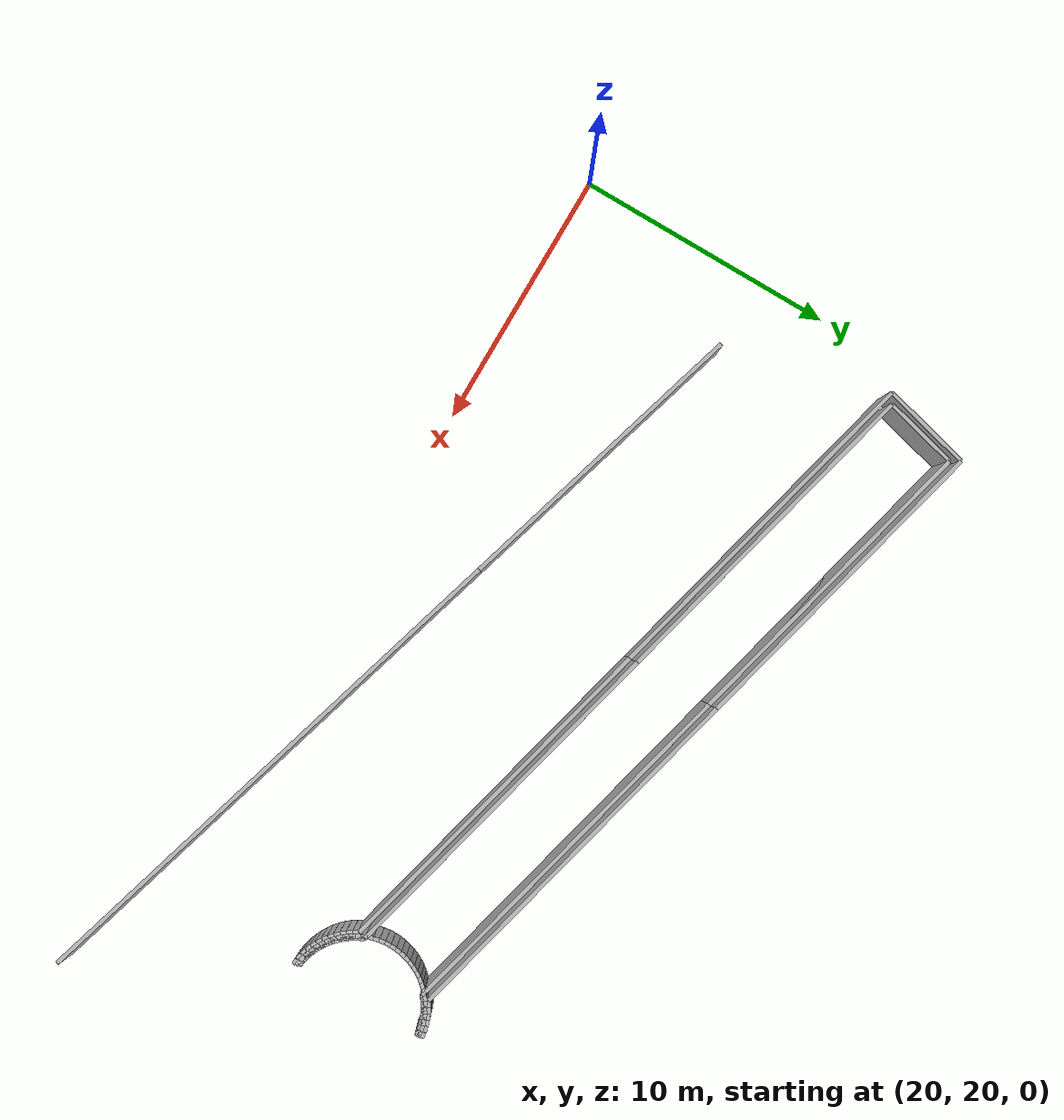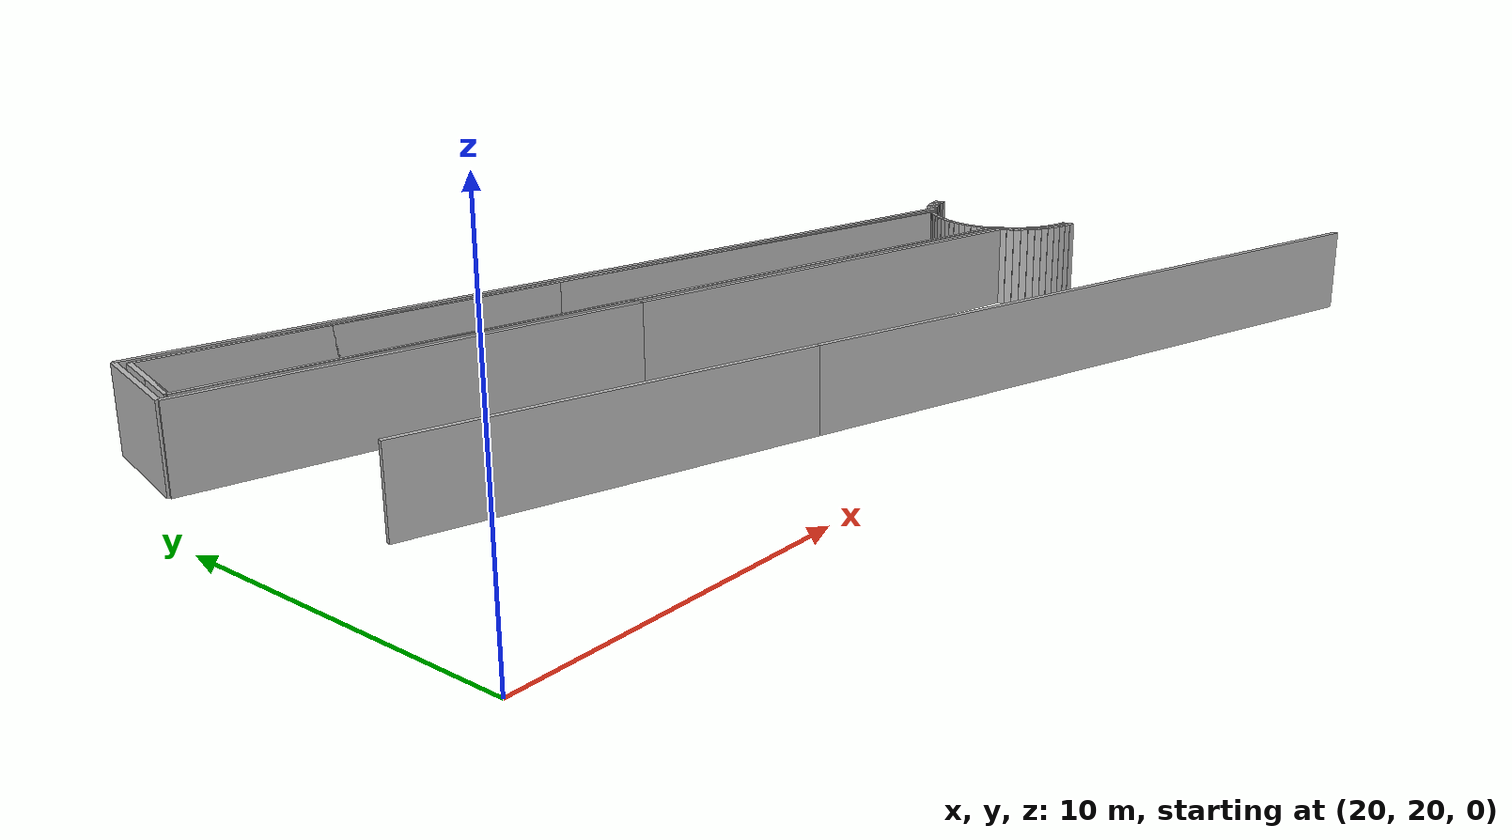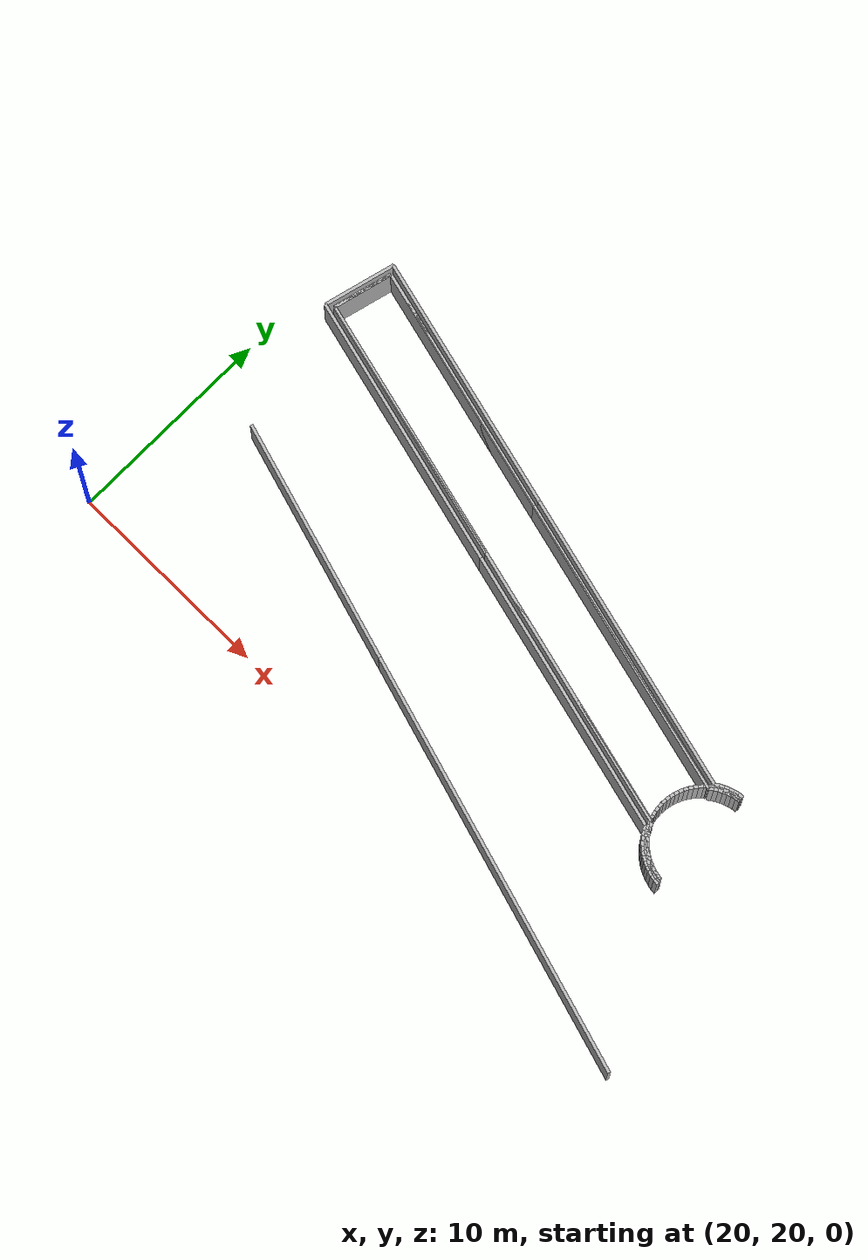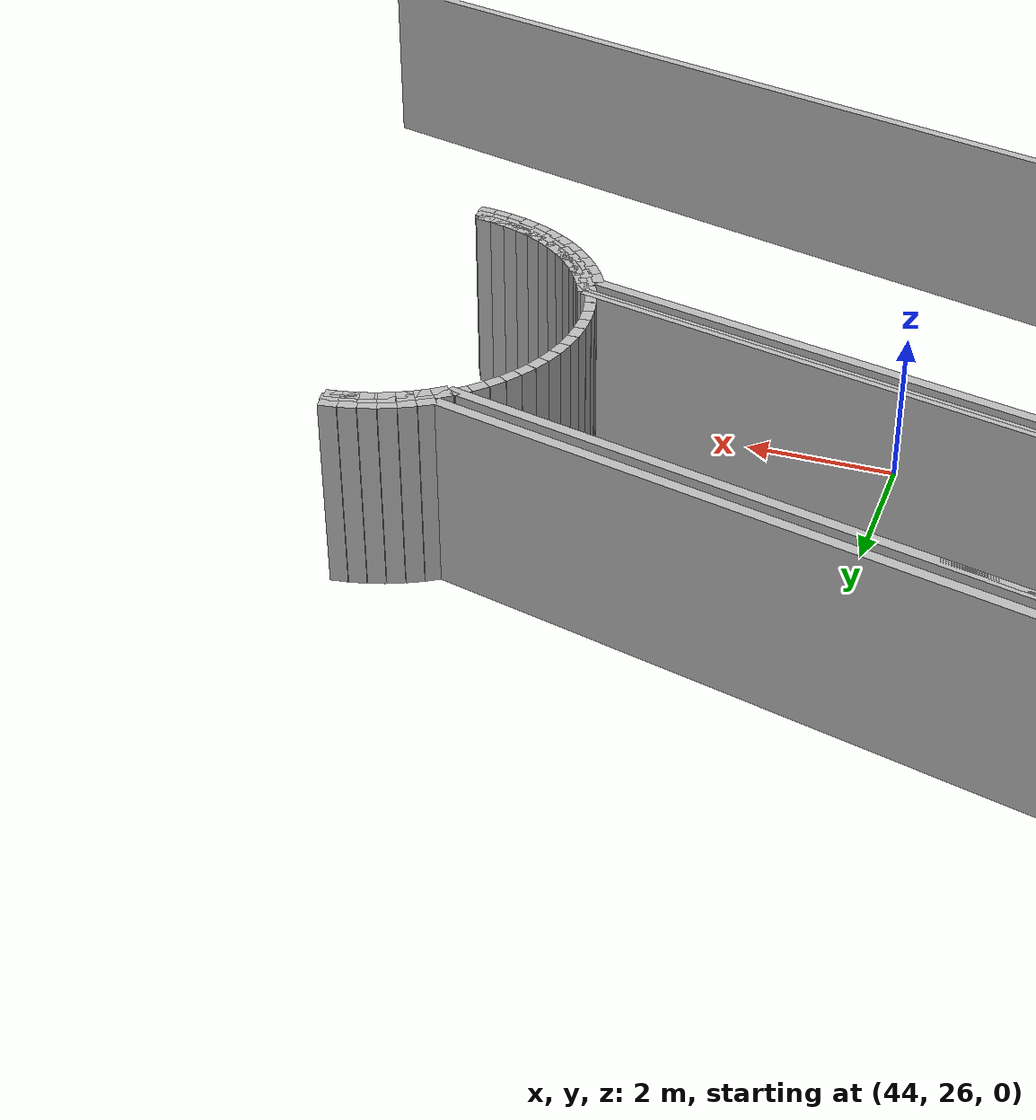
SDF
<?xml version="1.0" ?>
<sdf version="1.6">
  <model name="sps_0008">
    <pose frame="">0 0 0 0 -0 0</pose>
    <static>1</static>
    <self_collide>0</self_collide>
    <allow_auto_disable>0</allow_auto_disable>
    <link name="Wall0">
      <kinematic>0</kinematic>
      <gravity>1</gravity>
      <self_collide>0</self_collide>
      <collision name="collision">
        <geometry>
          <box>
            <size>13.9585 0.15 2.5</size>
          </box>
        </geometry>
        <pose frame="">0 0 0 0 -0 0</pose>
      </collision>
      <visual name="visual">
        <geometry>
          <box>
            <size>13.9585 0.15 2.5</size>
          </box>
        </geometry>
        <pose frame="">0 0 0 0 -0 0</pose>
        <cast_shadows>1</cast_shadows>
        <transparency>0.0</transparency>
      </visual>
      <pose frame="">41.2356 28.6875 1.25 0 -0 2.89383</pose>
    </link>
    <link name="Wall1">
      <kinematic>0</kinematic>
      <gravity>1</gravity>
      <self_collide>0</self_collide>
      <collision name="collision">
        <geometry>
          <box>
            <size>13.0248 0.15 2.5</size>
          </box>
        </geometry>
        <pose frame="">0 0 0 0 -0 0</pose>
      </collision>
      <visual name="visual">
        <geometry>
          <box>
            <size>13.0248 0.15 2.5</size>
          </box>
        </geometry>
        <pose frame="">0 0 0 0 -0 0</pose>
        <cast_shadows>1</cast_shadows>
        <transparency>0.0</transparency>
      </visual>
      <pose frame="">28.1559 31.9962 1.25 0 -0 2.89383</pose>
    </link>
    <link name="Wall2">
      <kinematic>0</kinematic>
      <gravity>1</gravity>
      <self_collide>0</self_collide>
      <collision name="collision">
        <geometry>
          <box>
            <size>14.6929 0.15 2.5</size>
          </box>
        </geometry>
        <pose frame="">0 0 0 0 -0 0</pose>
      </collision>
      <visual name="visual">
        <geometry>
          <box>
            <size>14.6929 0.15 2.5</size>
          </box>
        </geometry>
        <pose frame="">0 0 0 0 -0 0</pose>
        <cast_shadows>1</cast_shadows>
        <transparency>0.0</transparency>
      </visual>
      <pose frame="">41.5916 31.5887 1.25 0 -0 2.89386</pose>
    </link>
    <link name="Wall3">
      <kinematic>0</kinematic>
      <gravity>1</gravity>
      <self_collide>0</self_collide>
      <collision name="collision">
        <geometry>
          <box>
            <size>12.2908 0.15 2.5</size>
          </box>
        </geometry>
        <pose frame="">0 0 0 0 -0 0</pose>
      </collision>
      <visual name="visual">
        <geometry>
          <box>
            <size>12.2908 0.15 2.5</size>
          </box>
        </geometry>
        <pose frame="">0 0 0 0 -0 0</pose>
        <cast_shadows>1</cast_shadows>
        <transparency>0.0</transparency>
      </visual>
      <pose frame="">28.5116 34.897 1.25 0 -0 2.89386</pose>
    </link>
    <link name="Wall384">
      <kinematic>0</kinematic>
      <gravity>1</gravity>
      <self_collide>0</self_collide>
      <collision name="collision">
        <geometry>
          <box>
            <size>14.735 0.15 2.5</size>
          </box>
        </geometry>
        <pose frame="">0 0 0 0 -0 0</pose>
      </collision>
      <visual name="visual">
        <geometry>
          <box>
            <size>14.735 0.15 2.5</size>
          </box>
        </geometry>
        <pose frame="">0 0 0 0 -0 0</pose>
        <cast_shadows>1</cast_shadows>
        <transparency>0.0</transparency>
      </visual>
      <pose frame="">41.612 31.8926 1.25 0 -0 2.89384</pose>
    </link>
    <link name="Wall385">
      <kinematic>0</kinematic>
      <gravity>1</gravity>
      <self_collide>0</self_collide>
      <collision name="collision">
        <geometry>
          <box>
            <size>12.5149 0.15 2.5</size>
          </box>
        </geometry>
        <pose frame="">0 0 0 0 -0 0</pose>
      </collision>
      <visual name="visual">
        <geometry>
          <box>
            <size>12.5149 0.15 2.5</size>
          </box>
        </geometry>
        <pose frame="">0 0 0 0 -0 0</pose>
        <cast_shadows>1</cast_shadows>
        <transparency>0.0</transparency>
      </visual>
      <pose frame="">28.403 35.2338 1.25 0 -0 2.89384</pose>
    </link>
    <link name="Wall1122">
      <kinematic>0</kinematic>
      <gravity>1</gravity>
      <self_collide>0</self_collide>
      <collision name="collision">
        <geometry>
          <box>
            <size>2.89925 0.15 2.5</size>
          </box>
        </geometry>
        <pose frame="">0 0 0 0 -0 0</pose>
      </collision>
      <visual name="visual">
        <geometry>
          <box>
            <size>2.89925 0.15 2.5</size>
          </box>
        </geometry>
        <pose frame="">0 0 0 0 -0 0</pose>
        <cast_shadows>1</cast_shadows>
        <transparency>0.0</transparency>
      </visual>
      <pose frame="">22.1981 34.9986 1.25 0 0 -1.81871</pose>
    </link>
    <link name="Wall1452">
      <kinematic>0</kinematic>
      <gravity>1</gravity>
      <self_collide>0</self_collide>
      <collision name="collision">
        <geometry>
          <box>
            <size>11.8976 0.15 2.5</size>
          </box>
        </geometry>
        <pose frame="">0 0 0 0 -0 0</pose>
      </collision>
      <visual name="visual">
        <geometry>
          <box>
            <size>11.8976 0.15 2.5</size>
          </box>
        </geometry>
        <pose frame="">0 0 0 0 -0 0</pose>
        <cast_shadows>1</cast_shadows>
        <transparency>0.0</transparency>
      </visual>
      <pose frame="">28.7678 25.5044 1.25 0 0 -0.289232</pose>
    </link>
    <link name="Wall1453">
      <kinematic>0</kinematic>
      <gravity>1</gravity>
      <self_collide>0</self_collide>
      <collision name="collision">
        <geometry>
          <box>
            <size>20.7372 0.15 2.5</size>
          </box>
        </geometry>
        <pose frame="">0 0 0 0 -0 0</pose>
      </collision>
      <visual name="visual">
        <geometry>
          <box>
            <size>20.7372 0.15 2.5</size>
          </box>
        </geometry>
        <pose frame="">0 0 0 0 -0 0</pose>
        <cast_shadows>1</cast_shadows>
        <transparency>0.0</transparency>
      </visual>
      <pose frame="">44.4074 20.8504 1.25 0 0 -0.289232</pose>
    </link>
    <link name="Wall1740">
      <kinematic>0</kinematic>
      <gravity>1</gravity>
      <self_collide>0</self_collide>
      <collision name="collision">
        <geometry>
          <box>
            <size>13.4 0.15 2.5</size>
          </box>
        </geometry>
        <pose frame="">0 0 0 0 -0 0</pose>
      </collision>
      <visual name="visual">
        <geometry>
          <box>
            <size>13.4 0.15 2.5</size>
          </box>
        </geometry>
        <pose frame="">0 0 0 0 -0 0</pose>
        <cast_shadows>1</cast_shadows>
        <transparency>0.0</transparency>
      </visual>
      <pose frame="">27.9741 31.7326 1.25 0 0 -0.247762</pose>
    </link>
    <link name="Wall1741">
      <kinematic>0</kinematic>
      <gravity>1</gravity>
      <self_collide>0</self_collide>
      <collision name="collision">
        <geometry>
          <box>
            <size>13.8499 0.15 2.5</size>
          </box>
        </geometry>
        <pose frame="">0 0 0 0 -0 0</pose>
      </collision>
      <visual name="visual">
        <geometry>
          <box>
            <size>13.8499 0.15 2.5</size>
          </box>
        </geometry>
        <pose frame="">0 0 0 0 -0 0</pose>
        <cast_shadows>1</cast_shadows>
        <transparency>0.0</transparency>
      </visual>
      <pose frame="">41.1829 28.3913 1.25 0 0 -0.247762</pose>
    </link>
    <link name="Wall2461">
      <kinematic>0</kinematic>
      <gravity>1</gravity>
      <self_collide>0</self_collide>
      <collision name="collision">
        <geometry>
          <box>
            <size>3.49939 0.15 2.5</size>
          </box>
        </geometry>
        <pose frame="">0 0 0 0 -0 0</pose>
      </collision>
      <visual name="visual">
        <geometry>
          <box>
            <size>3.49939 0.15 2.5</size>
          </box>
        </geometry>
        <pose frame="">0 0 0 0 -0 0</pose>
        <cast_shadows>1</cast_shadows>
        <transparency>0.0</transparency>
      </visual>
      <pose frame="">21.9076 35.072 1.25 0 0 -1.8185</pose>
    </link>
    <link name="Wall3707">
      <kinematic>0</kinematic>
      <gravity>1</gravity>
      <self_collide>0</self_collide>
      <collision name="collision">
        <geometry>
          <box>
            <size>0.222486 0.15 2.5</size>
          </box>
        </geometry>
        <pose frame="">0 0 0 0 -0 0</pose>
      </collision>
      <visual name="visual">
        <geometry>
          <box>
            <size>0.222486 0.15 2.5</size>
          </box>
        </geometry>
        <pose frame="">0 0 0 0 -0 0</pose>
        <cast_shadows>1</cast_shadows>
        <transparency>0.0</transparency>
      </visual>
      <pose frame="">49.9536 25.368 1.25 0 -0 3.01064</pose>
    </link>
    <link name="Wall3708">
      <kinematic>0</kinematic>
      <gravity>1</gravity>
      <self_collide>0</self_collide>
      <collision name="collision">
        <geometry>
          <box>
            <size>0.222498 0.15 2.5</size>
          </box>
        </geometry>
        <pose frame="">0 0 0 0 -0 0</pose>
      </collision>
      <visual name="visual">
        <geometry>
          <box>
            <size>0.222498 0.15 2.5</size>
          </box>
        </geometry>
        <pose frame="">0 0 0 0 -0 0</pose>
        <cast_shadows>1</cast_shadows>
        <transparency>0.0</transparency>
      </visual>
      <pose frame="">49.7347 25.4066 1.25 0 -0 2.92343</pose>
    </link>
    <link name="Wall3709">
      <kinematic>0</kinematic>
      <gravity>1</gravity>
      <self_collide>0</self_collide>
      <collision name="collision">
        <geometry>
          <box>
            <size>0.222549 0.15 2.5</size>
          </box>
        </geometry>
        <pose frame="">0 0 0 0 -0 0</pose>
      </collision>
      <visual name="visual">
        <geometry>
          <box>
            <size>0.222549 0.15 2.5</size>
          </box>
        </geometry>
        <pose frame="">0 0 0 0 -0 0</pose>
        <cast_shadows>1</cast_shadows>
        <transparency>0.0</transparency>
      </visual>
      <pose frame="">49.52 25.4642 1.25 0 -0 2.83571</pose>
    </link>
    <link name="Wall3710">
      <kinematic>0</kinematic>
      <gravity>1</gravity>
      <self_collide>0</self_collide>
      <collision name="collision">
        <geometry>
          <box>
            <size>0.222356 0.15 2.5</size>
          </box>
        </geometry>
        <pose frame="">0 0 0 0 -0 0</pose>
      </collision>
      <visual name="visual">
        <geometry>
          <box>
            <size>0.222356 0.15 2.5</size>
          </box>
        </geometry>
        <pose frame="">0 0 0 0 -0 0</pose>
        <cast_shadows>1</cast_shadows>
        <transparency>0.0</transparency>
      </visual>
      <pose frame="">49.3111 25.5403 1.25 0 -0 2.74834</pose>
    </link>
    <link name="Wall3711">
      <kinematic>0</kinematic>
      <gravity>1</gravity>
      <self_collide>0</self_collide>
      <collision name="collision">
        <geometry>
          <box>
            <size>0.222545 0.15 2.5</size>
          </box>
        </geometry>
        <pose frame="">0 0 0 0 -0 0</pose>
      </collision>
      <visual name="visual">
        <geometry>
          <box>
            <size>0.222545 0.15 2.5</size>
          </box>
        </geometry>
        <pose frame="">0 0 0 0 -0 0</pose>
        <cast_shadows>1</cast_shadows>
        <transparency>0.0</transparency>
      </visual>
      <pose frame="">49.1098 25.6343 1.25 0 -0 2.66151</pose>
    </link>
    <link name="Wall3712">
      <kinematic>0</kinematic>
      <gravity>1</gravity>
      <self_collide>0</self_collide>
      <collision name="collision">
        <geometry>
          <box>
            <size>0.222361 0.15 2.5</size>
          </box>
        </geometry>
        <pose frame="">0 0 0 0 -0 0</pose>
      </collision>
      <visual name="visual">
        <geometry>
          <box>
            <size>0.222361 0.15 2.5</size>
          </box>
        </geometry>
        <pose frame="">0 0 0 0 -0 0</pose>
        <cast_shadows>1</cast_shadows>
        <transparency>0.0</transparency>
      </visual>
      <pose frame="">48.9174 25.7455 1.25 0 -0 2.57354</pose>
    </link>
    <link name="Wall3713">
      <kinematic>0</kinematic>
      <gravity>1</gravity>
      <self_collide>0</self_collide>
      <collision name="collision">
        <geometry>
          <box>
            <size>0.222498 0.15 2.5</size>
          </box>
        </geometry>
        <pose frame="">0 0 0 0 -0 0</pose>
      </collision>
      <visual name="visual">
        <geometry>
          <box>
            <size>0.222498 0.15 2.5</size>
          </box>
        </geometry>
        <pose frame="">0 0 0 0 -0 0</pose>
        <cast_shadows>1</cast_shadows>
        <transparency>0.0</transparency>
      </visual>
      <pose frame="">48.7353 25.873 1.25 0 -0 2.4875</pose>
    </link>
    <link name="Wall3714">
      <kinematic>0</kinematic>
      <gravity>1</gravity>
      <self_collide>0</self_collide>
      <collision name="collision">
        <geometry>
          <box>
            <size>0.222517 0.15 2.5</size>
          </box>
        </geometry>
        <pose frame="">0 0 0 0 -0 0</pose>
      </collision>
      <visual name="visual">
        <geometry>
          <box>
            <size>0.222517 0.15 2.5</size>
          </box>
        </geometry>
        <pose frame="">0 0 0 0 -0 0</pose>
        <cast_shadows>1</cast_shadows>
        <transparency>0.0</transparency>
      </visual>
      <pose frame="">48.5651 26.0159 1.25 0 -0 2.39946</pose>
    </link>
    <link name="Wall3715">
      <kinematic>0</kinematic>
      <gravity>1</gravity>
      <self_collide>0</self_collide>
      <collision name="collision">
        <geometry>
          <box>
            <size>0.222393 0.15 2.5</size>
          </box>
        </geometry>
        <pose frame="">0 0 0 0 -0 0</pose>
      </collision>
      <visual name="visual">
        <geometry>
          <box>
            <size>0.222393 0.15 2.5</size>
          </box>
        </geometry>
        <pose frame="">0 0 0 0 -0 0</pose>
        <cast_shadows>1</cast_shadows>
        <transparency>0.0</transparency>
      </visual>
      <pose frame="">48.408 26.1731 1.25 0 -0 2.31232</pose>
    </link>
    <link name="Wall3716">
      <kinematic>0</kinematic>
      <gravity>1</gravity>
      <self_collide>0</self_collide>
      <collision name="collision">
        <geometry>
          <box>
            <size>0.222546 0.15 2.5</size>
          </box>
        </geometry>
        <pose frame="">0 0 0 0 -0 0</pose>
      </collision>
      <visual name="visual">
        <geometry>
          <box>
            <size>0.222546 0.15 2.5</size>
          </box>
        </geometry>
        <pose frame="">0 0 0 0 -0 0</pose>
        <cast_shadows>1</cast_shadows>
        <transparency>0.0</transparency>
      </visual>
      <pose frame="">48.2652 26.3434 1.25 0 -0 2.22472</pose>
    </link>
    <link name="Wall3717">
      <kinematic>0</kinematic>
      <gravity>1</gravity>
      <self_collide>0</self_collide>
      <collision name="collision">
        <geometry>
          <box>
            <size>0.222333 0.15 2.5</size>
          </box>
        </geometry>
        <pose frame="">0 0 0 0 -0 0</pose>
      </collision>
      <visual name="visual">
        <geometry>
          <box>
            <size>0.222333 0.15 2.5</size>
          </box>
        </geometry>
        <pose frame="">0 0 0 0 -0 0</pose>
        <cast_shadows>1</cast_shadows>
        <transparency>0.0</transparency>
      </visual>
      <pose frame="">48.1378 26.5255 1.25 0 -0 2.13763</pose>
    </link>
    <link name="Wall3718">
      <kinematic>0</kinematic>
      <gravity>1</gravity>
      <self_collide>0</self_collide>
      <collision name="collision">
        <geometry>
          <box>
            <size>0.222573 0.15 2.5</size>
          </box>
        </geometry>
        <pose frame="">0 0 0 0 -0 0</pose>
      </collision>
      <visual name="visual">
        <geometry>
          <box>
            <size>0.222573 0.15 2.5</size>
          </box>
        </geometry>
        <pose frame="">0 0 0 0 -0 0</pose>
        <cast_shadows>1</cast_shadows>
        <transparency>0.0</transparency>
      </visual>
      <pose frame="">48.0267 26.718 1.25 0 -0 2.05112</pose>
    </link>
    <link name="Wall3719">
      <kinematic>0</kinematic>
      <gravity>1</gravity>
      <self_collide>0</self_collide>
      <collision name="collision">
        <geometry>
          <box>
            <size>0.222488 0.15 2.5</size>
          </box>
        </geometry>
        <pose frame="">0 0 0 0 -0 0</pose>
      </collision>
      <visual name="visual">
        <geometry>
          <box>
            <size>0.222488 0.15 2.5</size>
          </box>
        </geometry>
        <pose frame="">0 0 0 0 -0 0</pose>
        <cast_shadows>1</cast_shadows>
        <transparency>0.0</transparency>
      </visual>
      <pose frame="">47.9328 26.9195 1.25 0 -0 1.96261</pose>
    </link>
    <link name="Wall3720">
      <kinematic>0</kinematic>
      <gravity>1</gravity>
      <self_collide>0</self_collide>
      <collision name="collision">
        <geometry>
          <box>
            <size>0.222494 0.15 2.5</size>
          </box>
        </geometry>
        <pose frame="">0 0 0 0 -0 0</pose>
      </collision>
      <visual name="visual">
        <geometry>
          <box>
            <size>0.222494 0.15 2.5</size>
          </box>
        </geometry>
        <pose frame="">0 0 0 0 -0 0</pose>
        <cast_shadows>1</cast_shadows>
        <transparency>0.0</transparency>
      </visual>
      <pose frame="">47.8569 27.1284 1.25 0 -0 1.87589</pose>
    </link>
    <link name="Wall3721">
      <kinematic>0</kinematic>
      <gravity>1</gravity>
      <self_collide>0</self_collide>
      <collision name="collision">
        <geometry>
          <box>
            <size>0.222452 0.15 2.5</size>
          </box>
        </geometry>
        <pose frame="">0 0 0 0 -0 0</pose>
      </collision>
      <visual name="visual">
        <geometry>
          <box>
            <size>0.222452 0.15 2.5</size>
          </box>
        </geometry>
        <pose frame="">0 0 0 0 -0 0</pose>
        <cast_shadows>1</cast_shadows>
        <transparency>0.0</transparency>
      </visual>
      <pose frame="">47.7993 27.3431 1.25 0 -0 1.78929</pose>
    </link>
    <link name="Wall3722">
      <kinematic>0</kinematic>
      <gravity>1</gravity>
      <self_collide>0</self_collide>
      <collision name="collision">
        <geometry>
          <box>
            <size>0.222265 0.15 2.5</size>
          </box>
        </geometry>
        <pose frame="">0 0 0 0 -0 0</pose>
      </collision>
      <visual name="visual">
        <geometry>
          <box>
            <size>0.222265 0.15 2.5</size>
          </box>
        </geometry>
        <pose frame="">0 0 0 0 -0 0</pose>
        <cast_shadows>1</cast_shadows>
        <transparency>0.0</transparency>
      </visual>
      <pose frame="">47.7609 27.5619 1.25 0 -0 1.7005</pose>
    </link>
    <link name="Wall3723">
      <kinematic>0</kinematic>
      <gravity>1</gravity>
      <self_collide>0</self_collide>
      <collision name="collision">
        <geometry>
          <box>
            <size>0.222621 0.15 2.5</size>
          </box>
        </geometry>
        <pose frame="">0 0 0 0 -0 0</pose>
      </collision>
      <visual name="visual">
        <geometry>
          <box>
            <size>0.222621 0.15 2.5</size>
          </box>
        </geometry>
        <pose frame="">0 0 0 0 -0 0</pose>
        <cast_shadows>1</cast_shadows>
        <transparency>0.0</transparency>
      </visual>
      <pose frame="">47.7417 27.7833 1.25 0 -0 1.61413</pose>
    </link>
    <link name="Wall3724">
      <kinematic>0</kinematic>
      <gravity>1</gravity>
      <self_collide>0</self_collide>
      <collision name="collision">
        <geometry>
          <box>
            <size>0.222438 0.15 2.5</size>
          </box>
        </geometry>
        <pose frame="">0 0 0 0 -0 0</pose>
      </collision>
      <visual name="visual">
        <geometry>
          <box>
            <size>0.222438 0.15 2.5</size>
          </box>
        </geometry>
        <pose frame="">0 0 0 0 -0 0</pose>
        <cast_shadows>1</cast_shadows>
        <transparency>0.0</transparency>
      </visual>
      <pose frame="">47.7417 28.0056 1.25 0 -0 1.52743</pose>
    </link>
    <link name="Wall3725">
      <kinematic>0</kinematic>
      <gravity>1</gravity>
      <self_collide>0</self_collide>
      <collision name="collision">
        <geometry>
          <box>
            <size>0.222502 0.15 2.5</size>
          </box>
        </geometry>
        <pose frame="">0 0 0 0 -0 0</pose>
      </collision>
      <visual name="visual">
        <geometry>
          <box>
            <size>0.222502 0.15 2.5</size>
          </box>
        </geometry>
        <pose frame="">0 0 0 0 -0 0</pose>
        <cast_shadows>1</cast_shadows>
        <transparency>0.0</transparency>
      </visual>
      <pose frame="">47.7611 28.227 1.25 0 -0 1.4393</pose>
    </link>
    <link name="Wall3726">
      <kinematic>0</kinematic>
      <gravity>1</gravity>
      <self_collide>0</self_collide>
      <collision name="collision">
        <geometry>
          <box>
            <size>0.222273 0.15 2.5</size>
          </box>
        </geometry>
        <pose frame="">0 0 0 0 -0 0</pose>
      </collision>
      <visual name="visual">
        <geometry>
          <box>
            <size>0.222273 0.15 2.5</size>
          </box>
        </geometry>
        <pose frame="">0 0 0 0 -0 0</pose>
        <cast_shadows>1</cast_shadows>
        <transparency>0.0</transparency>
      </visual>
      <pose frame="">47.7998 28.4458 1.25 0 -0 1.35213</pose>
    </link>
    <link name="Wall3727">
      <kinematic>0</kinematic>
      <gravity>1</gravity>
      <self_collide>0</self_collide>
      <collision name="collision">
        <geometry>
          <box>
            <size>0.222531 0.15 2.5</size>
          </box>
        </geometry>
        <pose frame="">0 0 0 0 -0 0</pose>
      </collision>
      <visual name="visual">
        <geometry>
          <box>
            <size>0.222531 0.15 2.5</size>
          </box>
        </geometry>
        <pose frame="">0 0 0 0 -0 0</pose>
        <cast_shadows>1</cast_shadows>
        <transparency>0.0</transparency>
      </visual>
      <pose frame="">47.8574 28.6604 1.25 0 -0 1.26518</pose>
    </link>
    <link name="Wall3728">
      <kinematic>0</kinematic>
      <gravity>1</gravity>
      <self_collide>0</self_collide>
      <collision name="collision">
        <geometry>
          <box>
            <size>0.222582 0.15 2.5</size>
          </box>
        </geometry>
        <pose frame="">0 0 0 0 -0 0</pose>
      </collision>
      <visual name="visual">
        <geometry>
          <box>
            <size>0.222582 0.15 2.5</size>
          </box>
        </geometry>
        <pose frame="">0 0 0 0 -0 0</pose>
        <cast_shadows>1</cast_shadows>
        <transparency>0.0</transparency>
      </visual>
      <pose frame="">47.9334 28.8693 1.25 0 -0 1.17797</pose>
    </link>
    <link name="Wall3729">
      <kinematic>0</kinematic>
      <gravity>1</gravity>
      <self_collide>0</self_collide>
      <collision name="collision">
        <geometry>
          <box>
            <size>0.222244 0.15 2.5</size>
          </box>
        </geometry>
        <pose frame="">0 0 0 0 -0 0</pose>
      </collision>
      <visual name="visual">
        <geometry>
          <box>
            <size>0.222244 0.15 2.5</size>
          </box>
        </geometry>
        <pose frame="">0 0 0 0 -0 0</pose>
        <cast_shadows>1</cast_shadows>
        <transparency>0.0</transparency>
      </visual>
      <pose frame="">48.0273 29.0707 1.25 0 -0 1.09094</pose>
    </link>
    <link name="Wall3730">
      <kinematic>0</kinematic>
      <gravity>1</gravity>
      <self_collide>0</self_collide>
      <collision name="collision">
        <geometry>
          <box>
            <size>0.222515 0.15 2.5</size>
          </box>
        </geometry>
        <pose frame="">0 0 0 0 -0 0</pose>
      </collision>
      <visual name="visual">
        <geometry>
          <box>
            <size>0.222515 0.15 2.5</size>
          </box>
        </geometry>
        <pose frame="">0 0 0 0 -0 0</pose>
        <cast_shadows>1</cast_shadows>
        <transparency>0.0</transparency>
      </visual>
      <pose frame="">48.1384 29.2631 1.25 0 -0 1.00318</pose>
    </link>
    <link name="Wall3731">
      <kinematic>0</kinematic>
      <gravity>1</gravity>
      <self_collide>0</self_collide>
      <collision name="collision">
        <geometry>
          <box>
            <size>0.222501 0.15 2.5</size>
          </box>
        </geometry>
        <pose frame="">0 0 0 0 -0 0</pose>
      </collision>
      <visual name="visual">
        <geometry>
          <box>
            <size>0.222501 0.15 2.5</size>
          </box>
        </geometry>
        <pose frame="">0 0 0 0 -0 0</pose>
        <cast_shadows>1</cast_shadows>
        <transparency>0.0</transparency>
      </visual>
      <pose frame="">48.2661 29.4451 1.25 0 -0 0.915335</pose>
    </link>
    <link name="Wall3732">
      <kinematic>0</kinematic>
      <gravity>1</gravity>
      <self_collide>0</self_collide>
      <collision name="collision">
        <geometry>
          <box>
            <size>0.222352 0.15 2.5</size>
          </box>
        </geometry>
        <pose frame="">0 0 0 0 -0 0</pose>
      </collision>
      <visual name="visual">
        <geometry>
          <box>
            <size>0.222352 0.15 2.5</size>
          </box>
        </geometry>
        <pose frame="">0 0 0 0 -0 0</pose>
        <cast_shadows>1</cast_shadows>
        <transparency>0.0</transparency>
      </visual>
      <pose frame="">48.409 29.6153 1.25 0 -0 0.829473</pose>
    </link>
    <link name="Wall3733">
      <kinematic>0</kinematic>
      <gravity>1</gravity>
      <self_collide>0</self_collide>
      <collision name="collision">
        <geometry>
          <box>
            <size>0.222697 0.15 2.5</size>
          </box>
        </geometry>
        <pose frame="">0 0 0 0 -0 0</pose>
      </collision>
      <visual name="visual">
        <geometry>
          <box>
            <size>0.222697 0.15 2.5</size>
          </box>
        </geometry>
        <pose frame="">0 0 0 0 -0 0</pose>
        <cast_shadows>1</cast_shadows>
        <transparency>0.0</transparency>
      </visual>
      <pose frame="">48.5662 29.7725 1.25 0 -0 0.741392</pose>
    </link>
    <link name="Wall3734">
      <kinematic>0</kinematic>
      <gravity>1</gravity>
      <self_collide>0</self_collide>
      <collision name="collision">
        <geometry>
          <box>
            <size>0.222241 0.15 2.5</size>
          </box>
        </geometry>
        <pose frame="">0 0 0 0 -0 0</pose>
      </collision>
      <visual name="visual">
        <geometry>
          <box>
            <size>0.222241 0.15 2.5</size>
          </box>
        </geometry>
        <pose frame="">0 0 0 0 -0 0</pose>
        <cast_shadows>1</cast_shadows>
        <transparency>0.0</transparency>
      </visual>
      <pose frame="">48.7365 29.9153 1.25 0 -0 0.653937</pose>
    </link>
    <link name="Wall3735">
      <kinematic>0</kinematic>
      <gravity>1</gravity>
      <self_collide>0</self_collide>
      <collision name="collision">
        <geometry>
          <box>
            <size>0.22267 0.15 2.5</size>
          </box>
        </geometry>
        <pose frame="">0 0 0 0 -0 0</pose>
      </collision>
      <visual name="visual">
        <geometry>
          <box>
            <size>0.22267 0.15 2.5</size>
          </box>
        </geometry>
        <pose frame="">0 0 0 0 -0 0</pose>
        <cast_shadows>1</cast_shadows>
        <transparency>0.0</transparency>
      </visual>
      <pose frame="">48.9186 30.0427 1.25 0 -0 0.567171</pose>
    </link>
    <link name="Wall3736">
      <kinematic>0</kinematic>
      <gravity>1</gravity>
      <self_collide>0</self_collide>
      <collision name="collision">
        <geometry>
          <box>
            <size>0.222298 0.15 2.5</size>
          </box>
        </geometry>
        <pose frame="">0 0 0 0 -0 0</pose>
      </collision>
      <visual name="visual">
        <geometry>
          <box>
            <size>0.222298 0.15 2.5</size>
          </box>
        </geometry>
        <pose frame="">0 0 0 0 -0 0</pose>
        <cast_shadows>1</cast_shadows>
        <transparency>0.0</transparency>
      </visual>
      <pose frame="">49.1111 30.1538 1.25 0 -0 0.479734</pose>
    </link>
    <link name="Wall3737">
      <kinematic>0</kinematic>
      <gravity>1</gravity>
      <self_collide>0</self_collide>
      <collision name="collision">
        <geometry>
          <box>
            <size>0.222455 0.15 2.5</size>
          </box>
        </geometry>
        <pose frame="">0 0 0 0 -0 0</pose>
      </collision>
      <visual name="visual">
        <geometry>
          <box>
            <size>0.222455 0.15 2.5</size>
          </box>
        </geometry>
        <pose frame="">0 0 0 0 -0 0</pose>
        <cast_shadows>1</cast_shadows>
        <transparency>0.0</transparency>
      </visual>
      <pose frame="">49.3125 30.2476 1.25 0 -0 0.392174</pose>
    </link>
    <link name="Wall3738">
      <kinematic>0</kinematic>
      <gravity>1</gravity>
      <self_collide>0</self_collide>
      <collision name="collision">
        <geometry>
          <box>
            <size>0.222531 0.15 2.5</size>
          </box>
        </geometry>
        <pose frame="">0 0 0 0 -0 0</pose>
      </collision>
      <visual name="visual">
        <geometry>
          <box>
            <size>0.222531 0.15 2.5</size>
          </box>
        </geometry>
        <pose frame="">0 0 0 0 -0 0</pose>
        <cast_shadows>1</cast_shadows>
        <transparency>0.0</transparency>
      </visual>
      <pose frame="">49.5214 30.3236 1.25 0 -0 0.305617</pose>
    </link>
    <link name="Wall3739">
      <kinematic>0</kinematic>
      <gravity>1</gravity>
      <self_collide>0</self_collide>
      <collision name="collision">
        <geometry>
          <box>
            <size>0.222412 0.15 2.5</size>
          </box>
        </geometry>
        <pose frame="">0 0 0 0 -0 0</pose>
      </collision>
      <visual name="visual">
        <geometry>
          <box>
            <size>0.222412 0.15 2.5</size>
          </box>
        </geometry>
        <pose frame="">0 0 0 0 -0 0</pose>
        <cast_shadows>1</cast_shadows>
        <transparency>0.0</transparency>
      </visual>
      <pose frame="">49.736 30.3811 1.25 0 -0 0.217687</pose>
    </link>
    <link name="Wall3740">
      <kinematic>0</kinematic>
      <gravity>1</gravity>
      <self_collide>0</self_collide>
      <collision name="collision">
        <geometry>
          <box>
            <size>0.222539 0.15 2.5</size>
          </box>
        </geometry>
        <pose frame="">0 0 0 0 -0 0</pose>
      </collision>
      <visual name="visual">
        <geometry>
          <box>
            <size>0.222539 0.15 2.5</size>
          </box>
        </geometry>
        <pose frame="">0 0 0 0 -0 0</pose>
        <cast_shadows>1</cast_shadows>
        <transparency>0.0</transparency>
      </visual>
      <pose frame="">49.9549 30.4196 1.25 0 -0 0.130648</pose>
    </link>
    <link name="Wall4597">
      <kinematic>0</kinematic>
      <gravity>1</gravity>
      <self_collide>0</self_collide>
      <collision name="collision">
        <geometry>
          <box>
            <size>0.220173 0.15 2.5</size>
          </box>
        </geometry>
        <pose frame="">0 0 0 0 -0 0</pose>
      </collision>
      <visual name="visual">
        <geometry>
          <box>
            <size>0.220173 0.15 2.5</size>
          </box>
        </geometry>
        <pose frame="">0 0 0 0 -0 0</pose>
        <cast_shadows>1</cast_shadows>
        <transparency>0.0</transparency>
      </visual>
      <pose frame="">49.9011 25.4703 1.25 0 -0 2.98292</pose>
    </link>
    <link name="Wall4598">
      <kinematic>0</kinematic>
      <gravity>1</gravity>
      <self_collide>0</self_collide>
      <collision name="collision">
        <geometry>
          <box>
            <size>0.220524 0.15 2.5</size>
          </box>
        </geometry>
        <pose frame="">0 0 0 0 -0 0</pose>
      </collision>
      <visual name="visual">
        <geometry>
          <box>
            <size>0.220524 0.15 2.5</size>
          </box>
        </geometry>
        <pose frame="">0 0 0 0 -0 0</pose>
        <cast_shadows>1</cast_shadows>
        <transparency>0.0</transparency>
      </visual>
      <pose frame="">49.6855 25.5147 1.25 0 -0 2.89413</pose>
    </link>
    <link name="Wall4599">
      <kinematic>0</kinematic>
      <gravity>1</gravity>
      <self_collide>0</self_collide>
      <collision name="collision">
        <geometry>
          <box>
            <size>0.220154 0.15 2.5</size>
          </box>
        </geometry>
        <pose frame="">0 0 0 0 -0 0</pose>
      </collision>
      <visual name="visual">
        <geometry>
          <box>
            <size>0.220154 0.15 2.5</size>
          </box>
        </geometry>
        <pose frame="">0 0 0 0 -0 0</pose>
        <cast_shadows>1</cast_shadows>
        <transparency>0.0</transparency>
      </visual>
      <pose frame="">49.4748 25.5781 1.25 0 -0 2.8045</pose>
    </link>
    <link name="Wall4600">
      <kinematic>0</kinematic>
      <gravity>1</gravity>
      <self_collide>0</self_collide>
      <collision name="collision">
        <geometry>
          <box>
            <size>0.220298 0.15 2.5</size>
          </box>
        </geometry>
        <pose frame="">0 0 0 0 -0 0</pose>
      </collision>
      <visual name="visual">
        <geometry>
          <box>
            <size>0.220298 0.15 2.5</size>
          </box>
        </geometry>
        <pose frame="">0 0 0 0 -0 0</pose>
        <cast_shadows>1</cast_shadows>
        <transparency>0.0</transparency>
      </visual>
      <pose frame="">49.2706 25.66 1.25 0 -0 2.71574</pose>
    </link>
    <link name="Wall4601">
      <kinematic>0</kinematic>
      <gravity>1</gravity>
      <self_collide>0</self_collide>
      <collision name="collision">
        <geometry>
          <box>
            <size>0.220378 0.15 2.5</size>
          </box>
        </geometry>
        <pose frame="">0 0 0 0 -0 0</pose>
      </collision>
      <visual name="visual">
        <geometry>
          <box>
            <size>0.220378 0.15 2.5</size>
          </box>
        </geometry>
        <pose frame="">0 0 0 0 -0 0</pose>
        <cast_shadows>1</cast_shadows>
        <transparency>0.0</transparency>
      </visual>
      <pose frame="">49.0744 25.7598 1.25 0 -0 2.6264</pose>
    </link>
    <link name="Wall4602">
      <kinematic>0</kinematic>
      <gravity>1</gravity>
      <self_collide>0</self_collide>
      <collision name="collision">
        <geometry>
          <box>
            <size>0.220248 0.15 2.5</size>
          </box>
        </geometry>
        <pose frame="">0 0 0 0 -0 0</pose>
      </collision>
      <visual name="visual">
        <geometry>
          <box>
            <size>0.220248 0.15 2.5</size>
          </box>
        </geometry>
        <pose frame="">0 0 0 0 -0 0</pose>
        <cast_shadows>1</cast_shadows>
        <transparency>0.0</transparency>
      </visual>
      <pose frame="">48.8879 25.8767 1.25 0 -0 2.53706</pose>
    </link>
    <link name="Wall4603">
      <kinematic>0</kinematic>
      <gravity>1</gravity>
      <self_collide>0</self_collide>
      <collision name="collision">
        <geometry>
          <box>
            <size>0.220423 0.15 2.5</size>
          </box>
        </geometry>
        <pose frame="">0 0 0 0 -0 0</pose>
      </collision>
      <visual name="visual">
        <geometry>
          <box>
            <size>0.220423 0.15 2.5</size>
          </box>
        </geometry>
        <pose frame="">0 0 0 0 -0 0</pose>
        <cast_shadows>1</cast_shadows>
        <transparency>0.0</transparency>
      </visual>
      <pose frame="">48.7125 26.0098 1.25 0 -0 2.44756</pose>
    </link>
    <link name="Wall4604">
      <kinematic>0</kinematic>
      <gravity>1</gravity>
      <self_collide>0</self_collide>
      <collision name="collision">
        <geometry>
          <box>
            <size>0.220454 0.15 2.5</size>
          </box>
        </geometry>
        <pose frame="">0 0 0 0 -0 0</pose>
      </collision>
      <visual name="visual">
        <geometry>
          <box>
            <size>0.220454 0.15 2.5</size>
          </box>
        </geometry>
        <pose frame="">0 0 0 0 -0 0</pose>
        <cast_shadows>1</cast_shadows>
        <transparency>0.0</transparency>
      </visual>
      <pose frame="">48.5496 26.158 1.25 0 -0 2.35933</pose>
    </link>
    <link name="Wall4605">
      <kinematic>0</kinematic>
      <gravity>1</gravity>
      <self_collide>0</self_collide>
      <collision name="collision">
        <geometry>
          <box>
            <size>0.220206 0.15 2.5</size>
          </box>
        </geometry>
        <pose frame="">0 0 0 0 -0 0</pose>
      </collision>
      <visual name="visual">
        <geometry>
          <box>
            <size>0.220206 0.15 2.5</size>
          </box>
        </geometry>
        <pose frame="">0 0 0 0 -0 0</pose>
        <cast_shadows>1</cast_shadows>
        <transparency>0.0</transparency>
      </visual>
      <pose frame="">48.4007 26.32 1.25 0 -0 2.26926</pose>
    </link>
    <link name="Wall4606">
      <kinematic>0</kinematic>
      <gravity>1</gravity>
      <self_collide>0</self_collide>
      <collision name="collision">
        <geometry>
          <box>
            <size>0.220339 0.15 2.5</size>
          </box>
        </geometry>
        <pose frame="">0 0 0 0 -0 0</pose>
      </collision>
      <visual name="visual">
        <geometry>
          <box>
            <size>0.220339 0.15 2.5</size>
          </box>
        </geometry>
        <pose frame="">0 0 0 0 -0 0</pose>
        <cast_shadows>1</cast_shadows>
        <transparency>0.0</transparency>
      </visual>
      <pose frame="">48.2667 26.4946 1.25 0 -0 2.18077</pose>
    </link>
    <link name="Wall4607">
      <kinematic>0</kinematic>
      <gravity>1</gravity>
      <self_collide>0</self_collide>
      <collision name="collision">
        <geometry>
          <box>
            <size>0.220331 0.15 2.5</size>
          </box>
        </geometry>
        <pose frame="">0 0 0 0 -0 0</pose>
      </collision>
      <visual name="visual">
        <geometry>
          <box>
            <size>0.220331 0.15 2.5</size>
          </box>
        </geometry>
        <pose frame="">0 0 0 0 -0 0</pose>
        <cast_shadows>1</cast_shadows>
        <transparency>0.0</transparency>
      </visual>
      <pose frame="">48.1489 26.6805 1.25 0 -0 2.09121</pose>
    </link>
    <link name="Wall4608">
      <kinematic>0</kinematic>
      <gravity>1</gravity>
      <self_collide>0</self_collide>
      <collision name="collision">
        <geometry>
          <box>
            <size>0.220417 0.15 2.5</size>
          </box>
        </geometry>
        <pose frame="">0 0 0 0 -0 0</pose>
      </collision>
      <visual name="visual">
        <geometry>
          <box>
            <size>0.220417 0.15 2.5</size>
          </box>
        </geometry>
        <pose frame="">0 0 0 0 -0 0</pose>
        <cast_shadows>1</cast_shadows>
        <transparency>0.0</transparency>
      </visual>
      <pose frame="">48.048 26.8762 1.25 0 -0 2.00249</pose>
    </link>
    <link name="Wall4609">
      <kinematic>0</kinematic>
      <gravity>1</gravity>
      <self_collide>0</self_collide>
      <collision name="collision">
        <geometry>
          <box>
            <size>26.9833 0.15 2.5</size>
          </box>
        </geometry>
        <pose frame="">0 0 0 0 -0 0</pose>
      </collision>
      <visual name="visual">
        <geometry>
          <box>
            <size>26.9833 0.15 2.5</size>
          </box>
        </geometry>
        <pose frame="">0 0 0 0 -0 0</pose>
        <cast_shadows>1</cast_shadows>
        <transparency>0.0</transparency>
      </visual>
      <pose frame="">34.9221 30.2848 1.25 0 -0 2.89384</pose>
    </link>
    <link name="Wall4610">
      <kinematic>0</kinematic>
      <gravity>1</gravity>
      <self_collide>0</self_collide>
      <collision name="collision">
        <geometry>
          <box>
            <size>2.89947 0.15 2.5</size>
          </box>
        </geometry>
        <pose frame="">0 0 0 0 -0 0</pose>
      </collision>
      <visual name="visual">
        <geometry>
          <box>
            <size>2.89947 0.15 2.5</size>
          </box>
        </geometry>
        <pose frame="">0 0 0 0 -0 0</pose>
        <cast_shadows>1</cast_shadows>
        <transparency>0.0</transparency>
      </visual>
      <pose frame="">22.1982 34.9987 1.25 0 -0 1.32284</pose>
    </link>
    <link name="Wall4611">
      <kinematic>0</kinematic>
      <gravity>1</gravity>
      <self_collide>0</self_collide>
      <collision name="collision">
        <geometry>
          <box>
            <size>26.9836 0.15 2.5</size>
          </box>
        </geometry>
        <pose frame="">0 0 0 0 -0 0</pose>
      </collision>
      <visual name="visual">
        <geometry>
          <box>
            <size>26.9836 0.15 2.5</size>
          </box>
        </geometry>
        <pose frame="">0 0 0 0 -0 0</pose>
        <cast_shadows>1</cast_shadows>
        <transparency>0.0</transparency>
      </visual>
      <pose frame="">35.6339 33.0958 1.25 0 0 -0.247734</pose>
    </link>
    <link name="Wall4612">
      <kinematic>0</kinematic>
      <gravity>1</gravity>
      <self_collide>0</self_collide>
      <collision name="collision">
        <geometry>
          <box>
            <size>0.210705 0.15 2.5</size>
          </box>
        </geometry>
        <pose frame="">0 0 0 0 -0 0</pose>
      </collision>
      <visual name="visual">
        <geometry>
          <box>
            <size>0.210705 0.15 2.5</size>
          </box>
        </geometry>
        <pose frame="">0 0 0 0 -0 0</pose>
        <cast_shadows>1</cast_shadows>
        <transparency>0.0</transparency>
      </visual>
      <pose frame="">48.7974 29.8516 1.25 0 -0 0.653929</pose>
    </link>
    <link name="Wall4613">
      <kinematic>0</kinematic>
      <gravity>1</gravity>
      <self_collide>0</self_collide>
      <collision name="collision">
        <geometry>
          <box>
            <size>0.210728 0.15 2.5</size>
          </box>
        </geometry>
        <pose frame="">0 0 0 0 -0 0</pose>
      </collision>
      <visual name="visual">
        <geometry>
          <box>
            <size>0.210728 0.15 2.5</size>
          </box>
        </geometry>
        <pose frame="">0 0 0 0 -0 0</pose>
        <cast_shadows>1</cast_shadows>
        <transparency>0.0</transparency>
      </visual>
      <pose frame="">48.9699 29.9724 1.25 0 -0 0.56824</pose>
    </link>
    <link name="Wall4614">
      <kinematic>0</kinematic>
      <gravity>1</gravity>
      <self_collide>0</self_collide>
      <collision name="collision">
        <geometry>
          <box>
            <size>0.210758 0.15 2.5</size>
          </box>
        </geometry>
        <pose frame="">0 0 0 0 -0 0</pose>
      </collision>
      <visual name="visual">
        <geometry>
          <box>
            <size>0.210758 0.15 2.5</size>
          </box>
        </geometry>
        <pose frame="">0 0 0 0 -0 0</pose>
        <cast_shadows>1</cast_shadows>
        <transparency>0.0</transparency>
      </visual>
      <pose frame="">49.1521 30.0779 1.25 0 -0 0.48178</pose>
    </link>
    <link name="Wall4615">
      <kinematic>0</kinematic>
      <gravity>1</gravity>
      <self_collide>0</self_collide>
      <collision name="collision">
        <geometry>
          <box>
            <size>0.210665 0.15 2.5</size>
          </box>
        </geometry>
        <pose frame="">0 0 0 0 -0 0</pose>
      </collision>
      <visual name="visual">
        <geometry>
          <box>
            <size>0.210665 0.15 2.5</size>
          </box>
        </geometry>
        <pose frame="">0 0 0 0 -0 0</pose>
        <cast_shadows>1</cast_shadows>
        <transparency>0.0</transparency>
      </visual>
      <pose frame="">49.3426 30.1673 1.25 0 -0 0.395571</pose>
    </link>
    <link name="Wall4616">
      <kinematic>0</kinematic>
      <gravity>1</gravity>
      <self_collide>0</self_collide>
      <collision name="collision">
        <geometry>
          <box>
            <size>0.210822 0.15 2.5</size>
          </box>
        </geometry>
        <pose frame="">0 0 0 0 -0 0</pose>
      </collision>
      <visual name="visual">
        <geometry>
          <box>
            <size>0.210822 0.15 2.5</size>
          </box>
        </geometry>
        <pose frame="">0 0 0 0 -0 0</pose>
        <cast_shadows>1</cast_shadows>
        <transparency>0.0</transparency>
      </visual>
      <pose frame="">49.5402 30.24 1.25 0 -0 0.309482</pose>
    </link>
    <link name="Wall4617">
      <kinematic>0</kinematic>
      <gravity>1</gravity>
      <self_collide>0</self_collide>
      <collision name="collision">
        <geometry>
          <box>
            <size>0.210597 0.15 2.5</size>
          </box>
        </geometry>
        <pose frame="">0 0 0 0 -0 0</pose>
      </collision>
      <visual name="visual">
        <geometry>
          <box>
            <size>0.210597 0.15 2.5</size>
          </box>
        </geometry>
        <pose frame="">0 0 0 0 -0 0</pose>
        <cast_shadows>1</cast_shadows>
        <transparency>0.0</transparency>
      </visual>
      <pose frame="">49.7433 30.2954 1.25 0 -0 0.222976</pose>
    </link>
    <link name="Wall4618">
      <kinematic>0</kinematic>
      <gravity>1</gravity>
      <self_collide>0</self_collide>
      <collision name="collision">
        <geometry>
          <box>
            <size>0.210754 0.15 2.5</size>
          </box>
        </geometry>
        <pose frame="">0 0 0 0 -0 0</pose>
      </collision>
      <visual name="visual">
        <geometry>
          <box>
            <size>0.210754 0.15 2.5</size>
          </box>
        </geometry>
        <pose frame="">0 0 0 0 -0 0</pose>
        <cast_shadows>1</cast_shadows>
        <transparency>0.0</transparency>
      </visual>
      <pose frame="">49.9504 30.333 1.25 0 -0 0.136245</pose>
    </link>
    <link name="Wall5675">
      <kinematic>0</kinematic>
      <gravity>1</gravity>
      <self_collide>0</self_collide>
      <collision name="collision">
        <geometry>
          <box>
            <size>0.220173 0.15 2.5</size>
          </box>
        </geometry>
        <pose frame="">0 0 0 0 -0 0</pose>
      </collision>
      <visual name="visual">
        <geometry>
          <box>
            <size>0.220173 0.15 2.5</size>
          </box>
        </geometry>
        <pose frame="">0 0 0 0 -0 0</pose>
        <cast_shadows>1</cast_shadows>
        <transparency>0.0</transparency>
      </visual>
      <pose frame="">49.9008 25.4701 1.25 0 -0 2.98292</pose>
    </link>
    <link name="Wall5676">
      <kinematic>0</kinematic>
      <gravity>1</gravity>
      <self_collide>0</self_collide>
      <collision name="collision">
        <geometry>
          <box>
            <size>0.220346 0.15 2.5</size>
          </box>
        </geometry>
        <pose frame="">0 0 0 0 -0 0</pose>
      </collision>
      <visual name="visual">
        <geometry>
          <box>
            <size>0.220346 0.15 2.5</size>
          </box>
        </geometry>
        <pose frame="">0 0 0 0 -0 0</pose>
        <cast_shadows>1</cast_shadows>
        <transparency>0.0</transparency>
      </visual>
      <pose frame="">49.6853 25.5145 1.25 0 -0 2.89393</pose>
    </link>
    <link name="Wall5677">
      <kinematic>0</kinematic>
      <gravity>1</gravity>
      <self_collide>0</self_collide>
      <collision name="collision">
        <geometry>
          <box>
            <size>0.220364 0.15 2.5</size>
          </box>
        </geometry>
        <pose frame="">0 0 0 0 -0 0</pose>
      </collision>
      <visual name="visual">
        <geometry>
          <box>
            <size>0.220364 0.15 2.5</size>
          </box>
        </geometry>
        <pose frame="">0 0 0 0 -0 0</pose>
        <cast_shadows>1</cast_shadows>
        <transparency>0.0</transparency>
      </visual>
      <pose frame="">49.4744 25.5779 1.25 0 -0 2.80513</pose>
    </link>
    <link name="Wall5678">
      <kinematic>0</kinematic>
      <gravity>1</gravity>
      <self_collide>0</self_collide>
      <collision name="collision">
        <geometry>
          <box>
            <size>0.220242 0.15 2.5</size>
          </box>
        </geometry>
        <pose frame="">0 0 0 0 -0 0</pose>
      </collision>
      <visual name="visual">
        <geometry>
          <box>
            <size>0.220242 0.15 2.5</size>
          </box>
        </geometry>
        <pose frame="">0 0 0 0 -0 0</pose>
        <cast_shadows>1</cast_shadows>
        <transparency>0.0</transparency>
      </visual>
      <pose frame="">49.2702 25.6598 1.25 0 -0 2.71563</pose>
    </link>
    <link name="Wall5679">
      <kinematic>0</kinematic>
      <gravity>1</gravity>
      <self_collide>0</self_collide>
      <collision name="collision">
        <geometry>
          <box>
            <size>0.220302 0.15 2.5</size>
          </box>
        </geometry>
        <pose frame="">0 0 0 0 -0 0</pose>
      </collision>
      <visual name="visual">
        <geometry>
          <box>
            <size>0.220302 0.15 2.5</size>
          </box>
        </geometry>
        <pose frame="">0 0 0 0 -0 0</pose>
        <cast_shadows>1</cast_shadows>
        <transparency>0.0</transparency>
      </visual>
      <pose frame="">49.0741 25.7596 1.25 0 -0 2.62588</pose>
    </link>
    <link name="Wall5680">
      <kinematic>0</kinematic>
      <gravity>1</gravity>
      <self_collide>0</self_collide>
      <collision name="collision">
        <geometry>
          <box>
            <size>0.220398 0.15 2.5</size>
          </box>
        </geometry>
        <pose frame="">0 0 0 0 -0 0</pose>
      </collision>
      <visual name="visual">
        <geometry>
          <box>
            <size>0.220398 0.15 2.5</size>
          </box>
        </geometry>
        <pose frame="">0 0 0 0 -0 0</pose>
        <cast_shadows>1</cast_shadows>
        <transparency>0.0</transparency>
      </visual>
      <pose frame="">48.8875 25.8765 1.25 0 -0 2.53754</pose>
    </link>
    <link name="Wall5681">
      <kinematic>0</kinematic>
      <gravity>1</gravity>
      <self_collide>0</self_collide>
      <collision name="collision">
        <geometry>
          <box>
            <size>0.220376 0.15 2.5</size>
          </box>
        </geometry>
        <pose frame="">0 0 0 0 -0 0</pose>
      </collision>
      <visual name="visual">
        <geometry>
          <box>
            <size>0.220376 0.15 2.5</size>
          </box>
        </geometry>
        <pose frame="">0 0 0 0 -0 0</pose>
        <cast_shadows>1</cast_shadows>
        <transparency>0.0</transparency>
      </visual>
      <pose frame="">48.7121 26.0096 1.25 0 -0 2.44739</pose>
    </link>
    <link name="Wall5682">
      <kinematic>0</kinematic>
      <gravity>1</gravity>
      <self_collide>0</self_collide>
      <collision name="collision">
        <geometry>
          <box>
            <size>0.220324 0.15 2.5</size>
          </box>
        </geometry>
        <pose frame="">0 0 0 0 -0 0</pose>
      </collision>
      <visual name="visual">
        <geometry>
          <box>
            <size>0.220324 0.15 2.5</size>
          </box>
        </geometry>
        <pose frame="">0 0 0 0 -0 0</pose>
        <cast_shadows>1</cast_shadows>
        <transparency>0.0</transparency>
      </visual>
      <pose frame="">48.5494 26.1578 1.25 0 -0 2.35874</pose>
    </link>
    <link name="Wall5683">
      <kinematic>0</kinematic>
      <gravity>1</gravity>
      <self_collide>0</self_collide>
      <collision name="collision">
        <geometry>
          <box>
            <size>0.220316 0.15 2.5</size>
          </box>
        </geometry>
        <pose frame="">0 0 0 0 -0 0</pose>
      </collision>
      <visual name="visual">
        <geometry>
          <box>
            <size>0.220316 0.15 2.5</size>
          </box>
        </geometry>
        <pose frame="">0 0 0 0 -0 0</pose>
        <cast_shadows>1</cast_shadows>
        <transparency>0.0</transparency>
      </visual>
      <pose frame="">48.4004 26.3198 1.25 0 -0 2.27029</pose>
    </link>
    <link name="Wall5684">
      <kinematic>0</kinematic>
      <gravity>1</gravity>
      <self_collide>0</self_collide>
      <collision name="collision">
        <geometry>
          <box>
            <size>0.220199 0.15 2.5</size>
          </box>
        </geometry>
        <pose frame="">0 0 0 0 -0 0</pose>
      </collision>
      <visual name="visual">
        <geometry>
          <box>
            <size>0.220199 0.15 2.5</size>
          </box>
        </geometry>
        <pose frame="">0 0 0 0 -0 0</pose>
        <cast_shadows>1</cast_shadows>
        <transparency>0.0</transparency>
      </visual>
      <pose frame="">48.2664 26.4944 1.25 0 -0 2.17986</pose>
    </link>
    <link name="Wall5685">
      <kinematic>0</kinematic>
      <gravity>1</gravity>
      <self_collide>0</self_collide>
      <collision name="collision">
        <geometry>
          <box>
            <size>0.220415 0.15 2.5</size>
          </box>
        </geometry>
        <pose frame="">0 0 0 0 -0 0</pose>
      </collision>
      <visual name="visual">
        <geometry>
          <box>
            <size>0.220415 0.15 2.5</size>
          </box>
        </geometry>
        <pose frame="">0 0 0 0 -0 0</pose>
        <cast_shadows>1</cast_shadows>
        <transparency>0.0</transparency>
      </visual>
      <pose frame="">48.1486 26.6803 1.25 0 -0 2.09132</pose>
    </link>
    <link name="Wall5686">
      <kinematic>0</kinematic>
      <gravity>1</gravity>
      <self_collide>0</self_collide>
      <collision name="collision">
        <geometry>
          <box>
            <size>0.220225 0.15 2.5</size>
          </box>
        </geometry>
        <pose frame="">0 0 0 0 -0 0</pose>
      </collision>
      <visual name="visual">
        <geometry>
          <box>
            <size>0.220225 0.15 2.5</size>
          </box>
        </geometry>
        <pose frame="">0 0 0 0 -0 0</pose>
        <cast_shadows>1</cast_shadows>
        <transparency>0.0</transparency>
      </visual>
      <pose frame="">48.0478 26.8759 1.25 0 -0 2.00258</pose>
    </link>
    <link name="Wall5687">
      <kinematic>0</kinematic>
      <gravity>1</gravity>
      <self_collide>0</self_collide>
      <collision name="collision">
        <geometry>
          <box>
            <size>26.9832 0.15 2.5</size>
          </box>
        </geometry>
        <pose frame="">0 0 0 0 -0 0</pose>
      </collision>
      <visual name="visual">
        <geometry>
          <box>
            <size>26.9832 0.15 2.5</size>
          </box>
        </geometry>
        <pose frame="">0 0 0 0 -0 0</pose>
        <cast_shadows>1</cast_shadows>
        <transparency>0.0</transparency>
      </visual>
      <pose frame="">34.922 30.2846 1.25 0 -0 2.89383</pose>
    </link>
    <link name="Wall5688">
      <kinematic>0</kinematic>
      <gravity>1</gravity>
      <self_collide>0</self_collide>
      <collision name="collision">
        <geometry>
          <box>
            <size>2.89925 0.15 2.5</size>
          </box>
        </geometry>
        <pose frame="">0 0 0 0 -0 0</pose>
      </collision>
      <visual name="visual">
        <geometry>
          <box>
            <size>2.89925 0.15 2.5</size>
          </box>
        </geometry>
        <pose frame="">0 0 0 0 -0 0</pose>
        <cast_shadows>1</cast_shadows>
        <transparency>0.0</transparency>
      </visual>
      <pose frame="">22.1981 34.9986 1.25 0 -0 1.32288</pose>
    </link>
    <link name="Wall5689">
      <kinematic>0</kinematic>
      <gravity>1</gravity>
      <self_collide>0</self_collide>
      <collision name="collision">
        <geometry>
          <box>
            <size>26.9838 0.15 2.5</size>
          </box>
        </geometry>
        <pose frame="">0 0 0 0 -0 0</pose>
      </collision>
      <visual name="visual">
        <geometry>
          <box>
            <size>26.9838 0.15 2.5</size>
          </box>
        </geometry>
        <pose frame="">0 0 0 0 -0 0</pose>
        <cast_shadows>1</cast_shadows>
        <transparency>0.0</transparency>
      </visual>
      <pose frame="">35.6338 33.0956 1.25 0 0 -0.247732</pose>
    </link>
    <link name="Wall5690">
      <kinematic>0</kinematic>
      <gravity>1</gravity>
      <self_collide>0</self_collide>
      <collision name="collision">
        <geometry>
          <box>
            <size>0.21056 0.15 2.5</size>
          </box>
        </geometry>
        <pose frame="">0 0 0 0 -0 0</pose>
      </collision>
      <visual name="visual">
        <geometry>
          <box>
            <size>0.21056 0.15 2.5</size>
          </box>
        </geometry>
        <pose frame="">0 0 0 0 -0 0</pose>
        <cast_shadows>1</cast_shadows>
        <transparency>0.0</transparency>
      </visual>
      <pose frame="">48.7974 29.8514 1.25 0 -0 0.654458</pose>
    </link>
    <link name="Wall5691">
      <kinematic>0</kinematic>
      <gravity>1</gravity>
      <self_collide>0</self_collide>
      <collision name="collision">
        <geometry>
          <box>
            <size>0.210883 0.15 2.5</size>
          </box>
        </geometry>
        <pose frame="">0 0 0 0 -0 0</pose>
      </collision>
      <visual name="visual">
        <geometry>
          <box>
            <size>0.210883 0.15 2.5</size>
          </box>
        </geometry>
        <pose frame="">0 0 0 0 -0 0</pose>
        <cast_shadows>1</cast_shadows>
        <transparency>0.0</transparency>
      </visual>
      <pose frame="">48.9698 29.9722 1.25 0 -0 0.567773</pose>
    </link>
    <link name="Wall5692">
      <kinematic>0</kinematic>
      <gravity>1</gravity>
      <self_collide>0</self_collide>
      <collision name="collision">
        <geometry>
          <box>
            <size>0.210567 0.15 2.5</size>
          </box>
        </geometry>
        <pose frame="">0 0 0 0 -0 0</pose>
      </collision>
      <visual name="visual">
        <geometry>
          <box>
            <size>0.210567 0.15 2.5</size>
          </box>
        </geometry>
        <pose frame="">0 0 0 0 -0 0</pose>
        <cast_shadows>1</cast_shadows>
        <transparency>0.0</transparency>
      </visual>
      <pose frame="">49.152 30.0777 1.25 0 -0 0.481926</pose>
    </link>
    <link name="Wall5693">
      <kinematic>0</kinematic>
      <gravity>1</gravity>
      <self_collide>0</self_collide>
      <collision name="collision">
        <geometry>
          <box>
            <size>0.210858 0.15 2.5</size>
          </box>
        </geometry>
        <pose frame="">0 0 0 0 -0 0</pose>
      </collision>
      <visual name="visual">
        <geometry>
          <box>
            <size>0.210858 0.15 2.5</size>
          </box>
        </geometry>
        <pose frame="">0 0 0 0 -0 0</pose>
        <cast_shadows>1</cast_shadows>
        <transparency>0.0</transparency>
      </visual>
      <pose frame="">49.3426 30.1671 1.25 0 -0 0.395504</pose>
    </link>
    <link name="Wall5694">
      <kinematic>0</kinematic>
      <gravity>1</gravity>
      <self_collide>0</self_collide>
      <collision name="collision">
        <geometry>
          <box>
            <size>0.210629 0.15 2.5</size>
          </box>
        </geometry>
        <pose frame="">0 0 0 0 -0 0</pose>
      </collision>
      <visual name="visual">
        <geometry>
          <box>
            <size>0.210629 0.15 2.5</size>
          </box>
        </geometry>
        <pose frame="">0 0 0 0 -0 0</pose>
        <cast_shadows>1</cast_shadows>
        <transparency>0.0</transparency>
      </visual>
      <pose frame="">49.5402 30.2398 1.25 0 -0 0.309471</pose>
    </link>
    <link name="Wall5695">
      <kinematic>0</kinematic>
      <gravity>1</gravity>
      <self_collide>0</self_collide>
      <collision name="collision">
        <geometry>
          <box>
            <size>0.210789 0.15 2.5</size>
          </box>
        </geometry>
        <pose frame="">0 0 0 0 -0 0</pose>
      </collision>
      <visual name="visual">
        <geometry>
          <box>
            <size>0.210789 0.15 2.5</size>
          </box>
        </geometry>
        <pose frame="">0 0 0 0 -0 0</pose>
        <cast_shadows>1</cast_shadows>
        <transparency>0.0</transparency>
      </visual>
      <pose frame="">49.7432 30.2952 1.25 0 -0 0.223066</pose>
    </link>
    <link name="Wall5696">
      <kinematic>0</kinematic>
      <gravity>1</gravity>
      <self_collide>0</self_collide>
      <collision name="collision">
        <geometry>
          <box>
            <size>0.210779 0.15 2.5</size>
          </box>
        </geometry>
        <pose frame="">0 0 0 0 -0 0</pose>
      </collision>
      <visual name="visual">
        <geometry>
          <box>
            <size>0.210779 0.15 2.5</size>
          </box>
        </geometry>
        <pose frame="">0 0 0 0 -0 0</pose>
        <cast_shadows>1</cast_shadows>
        <transparency>0.0</transparency>
      </visual>
      <pose frame="">49.9504 30.3329 1.25 0 -0 0.137106</pose>
    </link>
    <link name="Wall6415">
      <kinematic>0</kinematic>
      <gravity>1</gravity>
      <self_collide>0</self_collide>
      <collision name="collision">
        <geometry>
          <box>
            <size>0.229276 0.15 2.5</size>
          </box>
        </geometry>
        <pose frame="">0 0 0 0 -0 0</pose>
      </collision>
      <visual name="visual">
        <geometry>
          <box>
            <size>0.229276 0.15 2.5</size>
          </box>
        </geometry>
        <pose frame="">0 0 0 0 -0 0</pose>
        <cast_shadows>1</cast_shadows>
        <transparency>0.0</transparency>
      </visual>
      <pose frame="">48.851 30.1478 1.25 0 -0 0.570282</pose>
    </link>
    <link name="Wall6416">
      <kinematic>0</kinematic>
      <gravity>1</gravity>
      <self_collide>0</self_collide>
      <collision name="collision">
        <geometry>
          <box>
            <size>0.229303 0.15 2.5</size>
          </box>
        </geometry>
        <pose frame="">0 0 0 0 -0 0</pose>
      </collision>
      <visual name="visual">
        <geometry>
          <box>
            <size>0.229303 0.15 2.5</size>
          </box>
        </geometry>
        <pose frame="">0 0 0 0 -0 0</pose>
        <cast_shadows>1</cast_shadows>
        <transparency>0.0</transparency>
      </visual>
      <pose frame="">49.049 30.263 1.25 0 -0 0.483647</pose>
    </link>
    <link name="Wall6417">
      <kinematic>0</kinematic>
      <gravity>1</gravity>
      <self_collide>0</self_collide>
      <collision name="collision">
        <geometry>
          <box>
            <size>0.229263 0.15 2.5</size>
          </box>
        </geometry>
        <pose frame="">0 0 0 0 -0 0</pose>
      </collision>
      <visual name="visual">
        <geometry>
          <box>
            <size>0.229263 0.15 2.5</size>
          </box>
        </geometry>
        <pose frame="">0 0 0 0 -0 0</pose>
        <cast_shadows>1</cast_shadows>
        <transparency>0.0</transparency>
      </visual>
      <pose frame="">49.2562 30.3607 1.25 0 -0 0.397761</pose>
    </link>
    <link name="Wall6418">
      <kinematic>0</kinematic>
      <gravity>1</gravity>
      <self_collide>0</self_collide>
      <collision name="collision">
        <geometry>
          <box>
            <size>0.229156 0.15 2.5</size>
          </box>
        </geometry>
        <pose frame="">0 0 0 0 -0 0</pose>
      </collision>
      <visual name="visual">
        <geometry>
          <box>
            <size>0.229156 0.15 2.5</size>
          </box>
        </geometry>
        <pose frame="">0 0 0 0 -0 0</pose>
        <cast_shadows>1</cast_shadows>
        <transparency>0.0</transparency>
      </visual>
      <pose frame="">49.4709 30.4401 1.25 0 -0 0.310464</pose>
    </link>
    <link name="Wall6419">
      <kinematic>0</kinematic>
      <gravity>1</gravity>
      <self_collide>0</self_collide>
      <collision name="collision">
        <geometry>
          <box>
            <size>0.229367 0.15 2.5</size>
          </box>
        </geometry>
        <pose frame="">0 0 0 0 -0 0</pose>
      </collision>
      <visual name="visual">
        <geometry>
          <box>
            <size>0.229367 0.15 2.5</size>
          </box>
        </geometry>
        <pose frame="">0 0 0 0 -0 0</pose>
        <cast_shadows>1</cast_shadows>
        <transparency>0.0</transparency>
      </visual>
      <pose frame="">49.6919 30.5006 1.25 0 -0 0.224066</pose>
    </link>
    <link name="Wall6420">
      <kinematic>0</kinematic>
      <gravity>1</gravity>
      <self_collide>0</self_collide>
      <collision name="collision">
        <geometry>
          <box>
            <size>0.229181 0.15 2.5</size>
          </box>
        </geometry>
        <pose frame="">0 0 0 0 -0 0</pose>
      </collision>
      <visual name="visual">
        <geometry>
          <box>
            <size>0.229181 0.15 2.5</size>
          </box>
        </geometry>
        <pose frame="">0 0 0 0 -0 0</pose>
        <cast_shadows>1</cast_shadows>
        <transparency>0.0</transparency>
      </visual>
      <pose frame="">49.9172 30.5419 1.25 0 -0 0.138394</pose>
    </link>
    <link name="Wall18859">
      <kinematic>0</kinematic>
      <gravity>1</gravity>
      <self_collide>0</self_collide>
      <collision name="collision">
        <geometry>
          <box>
            <size>0.21056 0.15 2.5</size>
          </box>
        </geometry>
        <pose frame="">0 0 0 0 -0 0</pose>
      </collision>
      <visual name="visual">
        <geometry>
          <box>
            <size>0.21056 0.15 2.5</size>
          </box>
        </geometry>
        <pose frame="">0 0 0 0 -0 0</pose>
        <cast_shadows>1</cast_shadows>
        <transparency>0.0</transparency>
      </visual>
      <pose frame="">48.7974 29.8514 1.25 0 -0 0.654458</pose>
    </link>
    <link name="Wall18860">
      <kinematic>0</kinematic>
      <gravity>1</gravity>
      <self_collide>0</self_collide>
      <collision name="collision">
        <geometry>
          <box>
            <size>0.210883 0.15 2.5</size>
          </box>
        </geometry>
        <pose frame="">0 0 0 0 -0 0</pose>
      </collision>
      <visual name="visual">
        <geometry>
          <box>
            <size>0.210883 0.15 2.5</size>
          </box>
        </geometry>
        <pose frame="">0 0 0 0 -0 0</pose>
        <cast_shadows>1</cast_shadows>
        <transparency>0.0</transparency>
      </visual>
      <pose frame="">48.9698 29.9722 1.25 0 -0 0.567773</pose>
    </link>
    <link name="Wall18861">
      <kinematic>0</kinematic>
      <gravity>1</gravity>
      <self_collide>0</self_collide>
      <collision name="collision">
        <geometry>
          <box>
            <size>0.210567 0.15 2.5</size>
          </box>
        </geometry>
        <pose frame="">0 0 0 0 -0 0</pose>
      </collision>
      <visual name="visual">
        <geometry>
          <box>
            <size>0.210567 0.15 2.5</size>
          </box>
        </geometry>
        <pose frame="">0 0 0 0 -0 0</pose>
        <cast_shadows>1</cast_shadows>
        <transparency>0.0</transparency>
      </visual>
      <pose frame="">49.152 30.0777 1.25 0 -0 0.481926</pose>
    </link>
    <link name="Wall18862">
      <kinematic>0</kinematic>
      <gravity>1</gravity>
      <self_collide>0</self_collide>
      <collision name="collision">
        <geometry>
          <box>
            <size>0.210858 0.15 2.5</size>
          </box>
        </geometry>
        <pose frame="">0 0 0 0 -0 0</pose>
      </collision>
      <visual name="visual">
        <geometry>
          <box>
            <size>0.210858 0.15 2.5</size>
          </box>
        </geometry>
        <pose frame="">0 0 0 0 -0 0</pose>
        <cast_shadows>1</cast_shadows>
        <transparency>0.0</transparency>
      </visual>
      <pose frame="">49.3426 30.1671 1.25 0 -0 0.395504</pose>
    </link>
    <link name="Wall18863">
      <kinematic>0</kinematic>
      <gravity>1</gravity>
      <self_collide>0</self_collide>
      <collision name="collision">
        <geometry>
          <box>
            <size>0.210573 0.15 2.5</size>
          </box>
        </geometry>
        <pose frame="">0 0 0 0 -0 0</pose>
      </collision>
      <visual name="visual">
        <geometry>
          <box>
            <size>0.210573 0.15 2.5</size>
          </box>
        </geometry>
        <pose frame="">0 0 0 0 -0 0</pose>
        <cast_shadows>1</cast_shadows>
        <transparency>0.0</transparency>
      </visual>
      <pose frame="">49.5402 30.2397 1.25 0 -0 0.308643</pose>
    </link>
    <link name="Wall18864">
      <kinematic>0</kinematic>
      <gravity>1</gravity>
      <self_collide>0</self_collide>
      <collision name="collision">
        <geometry>
          <box>
            <size>0.210789 0.15 2.5</size>
          </box>
        </geometry>
        <pose frame="">0 0 0 0 -0 0</pose>
      </collision>
      <visual name="visual">
        <geometry>
          <box>
            <size>0.210789 0.15 2.5</size>
          </box>
        </geometry>
        <pose frame="">0 0 0 0 -0 0</pose>
        <cast_shadows>1</cast_shadows>
        <transparency>0.0</transparency>
      </visual>
      <pose frame="">49.7432 30.295 1.25 0 -0 0.223066</pose>
    </link>
    <link name="Wall18865">
      <kinematic>0</kinematic>
      <gravity>1</gravity>
      <self_collide>0</self_collide>
      <collision name="collision">
        <geometry>
          <box>
            <size>0.210779 0.15 2.5</size>
          </box>
        </geometry>
        <pose frame="">0 0 0 0 -0 0</pose>
      </collision>
      <visual name="visual">
        <geometry>
          <box>
            <size>0.210779 0.15 2.5</size>
          </box>
        </geometry>
        <pose frame="">0 0 0 0 -0 0</pose>
        <cast_shadows>1</cast_shadows>
        <transparency>0.0</transparency>
      </visual>
      <pose frame="">49.9504 30.3327 1.25 0 -0 0.137106</pose>
    </link>
    <link name="Wall24359">
      <kinematic>0</kinematic>
      <gravity>1</gravity>
      <self_collide>0</self_collide>
      <collision name="collision">
        <geometry>
          <box>
            <size>0.220354 0.15 2.5</size>
          </box>
        </geometry>
        <pose frame="">0 0 0 0 -0 0</pose>
      </collision>
      <visual name="visual">
        <geometry>
          <box>
            <size>0.220354 0.15 2.5</size>
          </box>
        </geometry>
        <pose frame="">0 0 0 0 -0 0</pose>
        <cast_shadows>1</cast_shadows>
        <transparency>0.0</transparency>
      </visual>
      <pose frame="">49.9009 25.4703 1.25 0 -0 2.98305</pose>
    </link>
    <link name="Wall24360">
      <kinematic>0</kinematic>
      <gravity>1</gravity>
      <self_collide>0</self_collide>
      <collision name="collision">
        <geometry>
          <box>
            <size>0.220346 0.15 2.5</size>
          </box>
        </geometry>
        <pose frame="">0 0 0 0 -0 0</pose>
      </collision>
      <visual name="visual">
        <geometry>
          <box>
            <size>0.220346 0.15 2.5</size>
          </box>
        </geometry>
        <pose frame="">0 0 0 0 -0 0</pose>
        <cast_shadows>1</cast_shadows>
        <transparency>0.0</transparency>
      </visual>
      <pose frame="">49.6853 25.5147 1.25 0 -0 2.89393</pose>
    </link>
    <link name="Wall24361">
      <kinematic>0</kinematic>
      <gravity>1</gravity>
      <self_collide>0</self_collide>
      <collision name="collision">
        <geometry>
          <box>
            <size>0.220384 0.15 2.5</size>
          </box>
        </geometry>
        <pose frame="">0 0 0 0 -0 0</pose>
      </collision>
      <visual name="visual">
        <geometry>
          <box>
            <size>0.220384 0.15 2.5</size>
          </box>
        </geometry>
        <pose frame="">0 0 0 0 -0 0</pose>
        <cast_shadows>1</cast_shadows>
        <transparency>0.0</transparency>
      </visual>
      <pose frame="">49.4744 25.5781 1.25 0 -0 2.80487</pose>
    </link>
    <link name="Wall24362">
      <kinematic>0</kinematic>
      <gravity>1</gravity>
      <self_collide>0</self_collide>
      <collision name="collision">
        <geometry>
          <box>
            <size>0.220242 0.15 2.5</size>
          </box>
        </geometry>
        <pose frame="">0 0 0 0 -0 0</pose>
      </collision>
      <visual name="visual">
        <geometry>
          <box>
            <size>0.220242 0.15 2.5</size>
          </box>
        </geometry>
        <pose frame="">0 0 0 0 -0 0</pose>
        <cast_shadows>1</cast_shadows>
        <transparency>0.0</transparency>
      </visual>
      <pose frame="">49.2702 25.66 1.25 0 -0 2.71563</pose>
    </link>
    <link name="Wall24363">
      <kinematic>0</kinematic>
      <gravity>1</gravity>
      <self_collide>0</self_collide>
      <collision name="collision">
        <geometry>
          <box>
            <size>0.220272 0.15 2.5</size>
          </box>
        </geometry>
        <pose frame="">0 0 0 0 -0 0</pose>
      </collision>
      <visual name="visual">
        <geometry>
          <box>
            <size>0.220272 0.15 2.5</size>
          </box>
        </geometry>
        <pose frame="">0 0 0 0 -0 0</pose>
        <cast_shadows>1</cast_shadows>
        <transparency>0.0</transparency>
      </visual>
      <pose frame="">49.0741 25.7598 1.25 0 -0 2.62612</pose>
    </link>
    <link name="Wall24364">
      <kinematic>0</kinematic>
      <gravity>1</gravity>
      <self_collide>0</self_collide>
      <collision name="collision">
        <geometry>
          <box>
            <size>0.220398 0.15 2.5</size>
          </box>
        </geometry>
        <pose frame="">0 0 0 0 -0 0</pose>
      </collision>
      <visual name="visual">
        <geometry>
          <box>
            <size>0.220398 0.15 2.5</size>
          </box>
        </geometry>
        <pose frame="">0 0 0 0 -0 0</pose>
        <cast_shadows>1</cast_shadows>
        <transparency>0.0</transparency>
      </visual>
      <pose frame="">48.8875 25.8767 1.25 0 -0 2.53754</pose>
    </link>
    <link name="Wall24365">
      <kinematic>0</kinematic>
      <gravity>1</gravity>
      <self_collide>0</self_collide>
      <collision name="collision">
        <geometry>
          <box>
            <size>0.220118 0.15 2.5</size>
          </box>
        </geometry>
        <pose frame="">0 0 0 0 -0 0</pose>
      </collision>
      <visual name="visual">
        <geometry>
          <box>
            <size>0.220118 0.15 2.5</size>
          </box>
        </geometry>
        <pose frame="">0 0 0 0 -0 0</pose>
        <cast_shadows>1</cast_shadows>
        <transparency>0.0</transparency>
      </visual>
      <pose frame="">48.7122 26.0097 1.25 0 -0 2.44749</pose>
    </link>
    <link name="Wall24366">
      <kinematic>0</kinematic>
      <gravity>1</gravity>
      <self_collide>0</self_collide>
      <collision name="collision">
        <geometry>
          <box>
            <size>0.220324 0.15 2.5</size>
          </box>
        </geometry>
        <pose frame="">0 0 0 0 -0 0</pose>
      </collision>
      <visual name="visual">
        <geometry>
          <box>
            <size>0.220324 0.15 2.5</size>
          </box>
        </geometry>
        <pose frame="">0 0 0 0 -0 0</pose>
        <cast_shadows>1</cast_shadows>
        <transparency>0.0</transparency>
      </visual>
      <pose frame="">48.5496 26.1578 1.25 0 -0 2.35874</pose>
    </link>
    <link name="Wall24367">
      <kinematic>0</kinematic>
      <gravity>1</gravity>
      <self_collide>0</self_collide>
      <collision name="collision">
        <geometry>
          <box>
            <size>0.220277 0.15 2.5</size>
          </box>
        </geometry>
        <pose frame="">0 0 0 0 -0 0</pose>
      </collision>
      <visual name="visual">
        <geometry>
          <box>
            <size>0.220277 0.15 2.5</size>
          </box>
        </geometry>
        <pose frame="">0 0 0 0 -0 0</pose>
        <cast_shadows>1</cast_shadows>
        <transparency>0.0</transparency>
      </visual>
      <pose frame="">48.4006 26.3198 1.25 0 -0 2.27008</pose>
    </link>
    <link name="Wall24368">
      <kinematic>0</kinematic>
      <gravity>1</gravity>
      <self_collide>0</self_collide>
      <collision name="collision">
        <geometry>
          <box>
            <size>0.220339 0.15 2.5</size>
          </box>
        </geometry>
        <pose frame="">0 0 0 0 -0 0</pose>
      </collision>
      <visual name="visual">
        <geometry>
          <box>
            <size>0.220339 0.15 2.5</size>
          </box>
        </geometry>
        <pose frame="">0 0 0 0 -0 0</pose>
        <cast_shadows>1</cast_shadows>
        <transparency>0.0</transparency>
      </visual>
      <pose frame="">48.2666 26.4944 1.25 0 -0 2.18077</pose>
    </link>
    <link name="Wall24369">
      <kinematic>0</kinematic>
      <gravity>1</gravity>
      <self_collide>0</self_collide>
      <collision name="collision">
        <geometry>
          <box>
            <size>0.220415 0.15 2.5</size>
          </box>
        </geometry>
        <pose frame="">0 0 0 0 -0 0</pose>
      </collision>
      <visual name="visual">
        <geometry>
          <box>
            <size>0.220415 0.15 2.5</size>
          </box>
        </geometry>
        <pose frame="">0 0 0 0 -0 0</pose>
        <cast_shadows>1</cast_shadows>
        <transparency>0.0</transparency>
      </visual>
      <pose frame="">48.1486 26.6803 1.25 0 -0 2.09132</pose>
    </link>
    <link name="Wall24370">
      <kinematic>0</kinematic>
      <gravity>1</gravity>
      <self_collide>0</self_collide>
      <collision name="collision">
        <geometry>
          <box>
            <size>0.220225 0.15 2.5</size>
          </box>
        </geometry>
        <pose frame="">0 0 0 0 -0 0</pose>
      </collision>
      <visual name="visual">
        <geometry>
          <box>
            <size>0.220225 0.15 2.5</size>
          </box>
        </geometry>
        <pose frame="">0 0 0 0 -0 0</pose>
        <cast_shadows>1</cast_shadows>
        <transparency>0.0</transparency>
      </visual>
      <pose frame="">48.0478 26.8759 1.25 0 -0 2.00258</pose>
    </link>
    <link name="Wall27373">
      <kinematic>0</kinematic>
      <gravity>1</gravity>
      <self_collide>0</self_collide>
      <collision name="collision">
        <geometry>
          <box>
            <size>0.228798 0.15 2.5</size>
          </box>
        </geometry>
        <pose frame="">0 0 0 0 -0 0</pose>
      </collision>
      <visual name="visual">
        <geometry>
          <box>
            <size>0.228798 0.15 2.5</size>
          </box>
        </geometry>
        <pose frame="">0 0 0 0 -0 0</pose>
        <cast_shadows>1</cast_shadows>
        <transparency>0.0</transparency>
      </visual>
      <pose frame="">49.9685 25.2461 1.25 0 -0 3.02233</pose>
    </link>
    <link name="Wall27374">
      <kinematic>0</kinematic>
      <gravity>1</gravity>
      <self_collide>0</self_collide>
      <collision name="collision">
        <geometry>
          <box>
            <size>0.229065 0.15 2.5</size>
          </box>
        </geometry>
        <pose frame="">0 0 0 0 -0 0</pose>
      </collision>
      <visual name="visual">
        <geometry>
          <box>
            <size>0.229065 0.15 2.5</size>
          </box>
        </geometry>
        <pose frame="">0 0 0 0 -0 0</pose>
        <cast_shadows>1</cast_shadows>
        <transparency>0.0</transparency>
      </visual>
      <pose frame="">49.7428 25.2831 1.25 0 -0 2.93605</pose>
    </link>
    <link name="Wall27375">
      <kinematic>0</kinematic>
      <gravity>1</gravity>
      <self_collide>0</self_collide>
      <collision name="collision">
        <geometry>
          <box>
            <size>0.228735 0.15 2.5</size>
          </box>
        </geometry>
        <pose frame="">0 0 0 0 -0 0</pose>
      </collision>
      <visual name="visual">
        <geometry>
          <box>
            <size>0.228735 0.15 2.5</size>
          </box>
        </geometry>
        <pose frame="">0 0 0 0 -0 0</pose>
        <cast_shadows>1</cast_shadows>
        <transparency>0.0</transparency>
      </visual>
      <pose frame="">49.521 25.3392 1.25 0 -0 2.85149</pose>
    </link>
    <link name="Wall27376">
      <kinematic>0</kinematic>
      <gravity>1</gravity>
      <self_collide>0</self_collide>
      <collision name="collision">
        <geometry>
          <box>
            <size>0.228801 0.15 2.5</size>
          </box>
        </geometry>
        <pose frame="">0 0 0 0 -0 0</pose>
      </collision>
      <visual name="visual">
        <geometry>
          <box>
            <size>0.228801 0.15 2.5</size>
          </box>
        </geometry>
        <pose frame="">0 0 0 0 -0 0</pose>
        <cast_shadows>1</cast_shadows>
        <transparency>0.0</transparency>
      </visual>
      <pose frame="">49.305 25.4139 1.25 0 -0 2.76574</pose>
    </link>
    <link name="Wall27377">
      <kinematic>0</kinematic>
      <gravity>1</gravity>
      <self_collide>0</self_collide>
      <collision name="collision">
        <geometry>
          <box>
            <size>0.22893 0.15 2.5</size>
          </box>
        </geometry>
        <pose frame="">0 0 0 0 -0 0</pose>
      </collision>
      <visual name="visual">
        <geometry>
          <box>
            <size>0.22893 0.15 2.5</size>
          </box>
        </geometry>
        <pose frame="">0 0 0 0 -0 0</pose>
        <cast_shadows>1</cast_shadows>
        <transparency>0.0</transparency>
      </visual>
      <pose frame="">49.0962 25.5069 1.25 0 -0 2.67985</pose>
    </link>
    <link name="Wall27378">
      <kinematic>0</kinematic>
      <gravity>1</gravity>
      <self_collide>0</self_collide>
      <collision name="collision">
        <geometry>
          <box>
            <size>0.228885 0.15 2.5</size>
          </box>
        </geometry>
        <pose frame="">0 0 0 0 -0 0</pose>
      </collision>
      <visual name="visual">
        <geometry>
          <box>
            <size>0.228885 0.15 2.5</size>
          </box>
        </geometry>
        <pose frame="">0 0 0 0 -0 0</pose>
        <cast_shadows>1</cast_shadows>
        <transparency>0.0</transparency>
      </visual>
      <pose frame="">48.8959 25.6173 1.25 0 -0 2.59569</pose>
    </link>
    <link name="Wall27379">
      <kinematic>0</kinematic>
      <gravity>1</gravity>
      <self_collide>0</self_collide>
      <collision name="collision">
        <geometry>
          <box>
            <size>0.228984 0.15 2.5</size>
          </box>
        </geometry>
        <pose frame="">0 0 0 0 -0 0</pose>
      </collision>
      <visual name="visual">
        <geometry>
          <box>
            <size>0.228984 0.15 2.5</size>
          </box>
        </geometry>
        <pose frame="">0 0 0 0 -0 0</pose>
        <cast_shadows>1</cast_shadows>
        <transparency>0.0</transparency>
      </visual>
      <pose frame="">48.7056 25.7443 1.25 0 -0 2.51003</pose>
    </link>
    <link name="Wall27380">
      <kinematic>0</kinematic>
      <gravity>1</gravity>
      <self_collide>0</self_collide>
      <collision name="collision">
        <geometry>
          <box>
            <size>0.22875 0.15 2.5</size>
          </box>
        </geometry>
        <pose frame="">0 0 0 0 -0 0</pose>
      </collision>
      <visual name="visual">
        <geometry>
          <box>
            <size>0.22875 0.15 2.5</size>
          </box>
        </geometry>
        <pose frame="">0 0 0 0 -0 0</pose>
        <cast_shadows>1</cast_shadows>
        <transparency>0.0</transparency>
      </visual>
      <pose frame="">48.5271 25.8871 1.25 0 -0 2.42417</pose>
    </link>
    <link name="Wall27381">
      <kinematic>0</kinematic>
      <gravity>1</gravity>
      <self_collide>0</self_collide>
      <collision name="collision">
        <geometry>
          <box>
            <size>0.22886 0.15 2.5</size>
          </box>
        </geometry>
        <pose frame="">0 0 0 0 -0 0</pose>
      </collision>
      <visual name="visual">
        <geometry>
          <box>
            <size>0.22886 0.15 2.5</size>
          </box>
        </geometry>
        <pose frame="">0 0 0 0 -0 0</pose>
        <cast_shadows>1</cast_shadows>
        <transparency>0.0</transparency>
      </visual>
      <pose frame="">48.3614 26.0446 1.25 0 -0 2.33884</pose>
    </link>
    <link name="Wall27382">
      <kinematic>0</kinematic>
      <gravity>1</gravity>
      <self_collide>0</self_collide>
      <collision name="collision">
        <geometry>
          <box>
            <size>0.228911 0.15 2.5</size>
          </box>
        </geometry>
        <pose frame="">0 0 0 0 -0 0</pose>
      </collision>
      <visual name="visual">
        <geometry>
          <box>
            <size>0.228911 0.15 2.5</size>
          </box>
        </geometry>
        <pose frame="">0 0 0 0 -0 0</pose>
        <cast_shadows>1</cast_shadows>
        <transparency>0.0</transparency>
      </visual>
      <pose frame="">48.2097 26.2157 1.25 0 -0 2.25345</pose>
    </link>
    <link name="Wall27383">
      <kinematic>0</kinematic>
      <gravity>1</gravity>
      <self_collide>0</self_collide>
      <collision name="collision">
        <geometry>
          <box>
            <size>0.228862 0.15 2.5</size>
          </box>
        </geometry>
        <pose frame="">0 0 0 0 -0 0</pose>
      </collision>
      <visual name="visual">
        <geometry>
          <box>
            <size>0.228862 0.15 2.5</size>
          </box>
        </geometry>
        <pose frame="">0 0 0 0 -0 0</pose>
        <cast_shadows>1</cast_shadows>
        <transparency>0.0</transparency>
      </visual>
      <pose frame="">48.0731 26.3991 1.25 0 -0 2.16878</pose>
    </link>
    <link name="Wall27384">
      <kinematic>0</kinematic>
      <gravity>1</gravity>
      <self_collide>0</self_collide>
      <collision name="collision">
        <geometry>
          <box>
            <size>0.228793 0.15 2.5</size>
          </box>
        </geometry>
        <pose frame="">0 0 0 0 -0 0</pose>
      </collision>
      <visual name="visual">
        <geometry>
          <box>
            <size>0.228793 0.15 2.5</size>
          </box>
        </geometry>
        <pose frame="">0 0 0 0 -0 0</pose>
        <cast_shadows>1</cast_shadows>
        <transparency>0.0</transparency>
      </visual>
      <pose frame="">47.9525 26.5934 1.25 0 -0 2.08326</pose>
    </link>
  </model>
</sdf>
